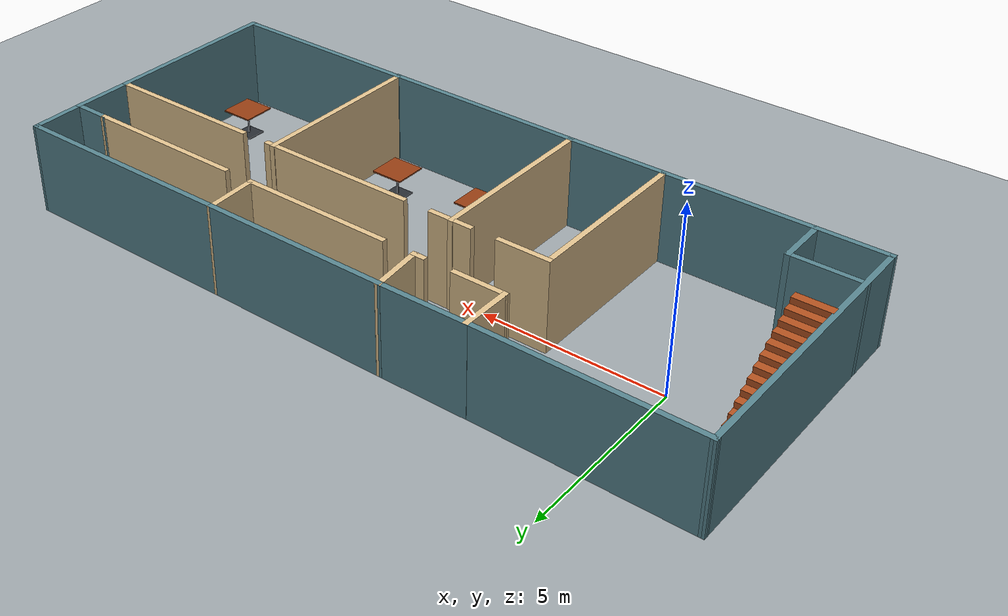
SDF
<?xml version="1.0" ?>
<sdf version='1.6'>
  <world name='default'>
    <light name='sun' type='directional'>
      <cast_shadows>1</cast_shadows>
      <pose>0 0 10 0 -0 0</pose>
      <diffuse>1 0.95 0.88 1</diffuse>
      <specular>0.25 0.25 0.25 1</specular>
      <attenuation>
        <range>1000</range>
        <constant>0.9</constant>
        <linear>0.01</linear>
        <quadratic>0.001</quadratic>
      </attenuation>
      <direction>0.5 0.1 -0.9</direction>
    </light>
    <scene>
      <ambient>0.68 0.68 0.68 1</ambient>
      <background>0.52 0.70 0.88 1</background>
      <shadows>1</shadows>
    </scene>
    <physics name='default_physics' default='0' type='ode'>
      <max_step_size>0.01</max_step_size>
      <real_time_factor>1</real_time_factor>
      <real_time_update_rate>100</real_time_update_rate>
    </physics>

    <!-- Gazebo Sim systems (ROS 2 / ros_gz) -->
    <plugin
      filename="gz-sim-physics-system"
      name="gz::sim::systems::Physics"/>

    <plugin
      filename="gz-sim-user-commands-system"
      name="gz::sim::systems::UserCommands"/>

    <plugin
      filename="gz-sim-scene-broadcaster-system"
      name="gz::sim::systems::SceneBroadcaster"/>

    <plugin
      filename="gz-sim-sensors-system"
      name="gz::sim::systems::Sensors">
      <render_engine>ogre2</render_engine>
    </plugin>
    <model name='ground_plane_0'>
      <static>1</static>
      <link name='link'>
        <collision name='collision'>
          <geometry>
            <plane>
              <normal>0 0 1</normal>
              <size>100 100</size>
            </plane>
          </geometry>
          <surface>
            <friction>
              <ode>
                <mu>100</mu>
                <mu2>50</mu2>
              </ode>
              <torsional>
                <ode/>
              </torsional>
            </friction>
            <bounce/>
            <contact>
              <ode/>
            </contact>
          </surface>
          <max_contacts>10</max_contacts>
        </collision>
        <visual name='visual'>
          <cast_shadows>0</cast_shadows>
          <geometry>
            <plane>
              <normal>0 0 1</normal>
              <size>100 100</size>
            </plane>
          </geometry>
          <material>
            <ambient>0.42 0.44 0.46 1</ambient>
            <diffuse>0.62 0.65 0.67 1</diffuse>
            <specular>0.08 0.08 0.08 1</specular>
            <emissive>0 0 0 1</emissive>
          </material>
        </visual>
        <velocity_decay>
          <linear>0</linear>
          <angular>0</angular>
        </velocity_decay>
        <self_collide>0</self_collide>
        <kinematic>0</kinematic>
        <gravity>1</gravity>
      </link>
      <pose>0.497681 0 0 0 -0 0</pose>
    </model>
    <gravity>0 0 -9.8</gravity>
    <magnetic_field>6e-06 2.3e-05 -4.2e-05</magnetic_field>
    <atmosphere type='adiabatic'/>
    <spherical_coordinates>
      <surface_model>EARTH_WGS84</surface_model>
      <latitude_deg>0</latitude_deg>
      <longitude_deg>0</longitude_deg>
      <elevation>0</elevation>
      <heading_deg>0</heading_deg>
    </spherical_coordinates>
    <model name='inco_planta_baja_0'>
      <link name='Stairs_0'>
        <pose>0 0 0 0 -0 0</pose>
        <self_collide>0</self_collide>
        <kinematic>0</kinematic>
        <visual name='Stairs_0_Visual_2'>
          <pose>-9.24623 1.59162 0.416667 0 -0 0</pose>
          <geometry>
            <box>
              <size>1 0.233333 0.166667</size>
            </box>
          </geometry>
                              <material>
            <ambient>0.25 0.12 0.05 1</ambient>
            <diffuse>0.70 0.32 0.12 1</diffuse>
            <specular>0.12 0.12 0.12 1</specular>
            <emissive>0 0 0 1</emissive>
          </material>
          <cast_shadows>1</cast_shadows>
          <transparency>0</transparency>
        </visual>
        <visual name='Stairs_0_Visual_0'>
          <pose>-9.24623 2.05829 0.083333 0 -0 0</pose>
          <geometry>
            <box>
              <size>1 0.233333 0.166667</size>
            </box>
          </geometry>
                              <material>
            <ambient>0.25 0.12 0.05 1</ambient>
            <diffuse>0.70 0.32 0.12 1</diffuse>
            <specular>0.12 0.12 0.12 1</specular>
            <emissive>0 0 0 1</emissive>
          </material>
          <cast_shadows>1</cast_shadows>
          <transparency>0</transparency>
        </visual>
        <visual name='Stairs_0_Visual_1'>
          <pose>-9.24623 1.82496 0.25 0 -0 0</pose>
          <geometry>
            <box>
              <size>1 0.233333 0.166667</size>
            </box>
          </geometry>
                              <material>
            <ambient>0.25 0.12 0.05 1</ambient>
            <diffuse>0.70 0.32 0.12 1</diffuse>
            <specular>0.12 0.12 0.12 1</specular>
            <emissive>0 0 0 1</emissive>
          </material>
          <cast_shadows>1</cast_shadows>
          <transparency>0</transparency>
        </visual>
        <visual name='Stairs_0_Visual_3'>
          <pose>-9.24623 1.35829 0.583333 0 -0 0</pose>
          <geometry>
            <box>
              <size>1 0.233333 0.166667</size>
            </box>
          </geometry>
                              <material>
            <ambient>0.25 0.12 0.05 1</ambient>
            <diffuse>0.70 0.32 0.12 1</diffuse>
            <specular>0.12 0.12 0.12 1</specular>
            <emissive>0 0 0 1</emissive>
          </material>
          <cast_shadows>1</cast_shadows>
          <transparency>0</transparency>
        </visual>
        <visual name='Stairs_0_Visual_4'>
          <pose>-9.24623 1.12495 0.75 0 -0 0</pose>
          <geometry>
            <box>
              <size>1 0.233333 0.166667</size>
            </box>
          </geometry>
                              <material>
            <ambient>0.25 0.12 0.05 1</ambient>
            <diffuse>0.70 0.32 0.12 1</diffuse>
            <specular>0.12 0.12 0.12 1</specular>
            <emissive>0 0 0 1</emissive>
          </material>
          <cast_shadows>1</cast_shadows>
          <transparency>0</transparency>
        </visual>
        <visual name='Stairs_0_Visual_5'>
          <pose>-9.24623 0.891622 0.916667 0 -0 0</pose>
          <geometry>
            <box>
              <size>1 0.233333 0.166667</size>
            </box>
          </geometry>
                              <material>
            <ambient>0.25 0.12 0.05 1</ambient>
            <diffuse>0.70 0.32 0.12 1</diffuse>
            <specular>0.12 0.12 0.12 1</specular>
            <emissive>0 0 0 1</emissive>
          </material>
          <cast_shadows>1</cast_shadows>
          <transparency>0</transparency>
        </visual>
        <visual name='Stairs_0_Visual_6'>
          <pose>-9.24623 0.658289 1.08333 0 -0 0</pose>
          <geometry>
            <box>
              <size>1 0.233333 0.166667</size>
            </box>
          </geometry>
                              <material>
            <ambient>0.25 0.12 0.05 1</ambient>
            <diffuse>0.70 0.32 0.12 1</diffuse>
            <specular>0.12 0.12 0.12 1</specular>
            <emissive>0 0 0 1</emissive>
          </material>
          <cast_shadows>1</cast_shadows>
          <transparency>0</transparency>
        </visual>
        <visual name='Stairs_0_Visual_8'>
          <pose>-9.24623 0.191622 1.41667 0 -0 0</pose>
          <geometry>
            <box>
              <size>1 0.233333 0.166667</size>
            </box>
          </geometry>
                              <material>
            <ambient>0.25 0.12 0.05 1</ambient>
            <diffuse>0.70 0.32 0.12 1</diffuse>
            <specular>0.12 0.12 0.12 1</specular>
            <emissive>0 0 0 1</emissive>
          </material>
          <cast_shadows>1</cast_shadows>
          <transparency>0</transparency>
        </visual>
        <visual name='Stairs_0_Visual_7'>
          <pose>-9.24623 0.424955 1.25 0 -0 0</pose>
          <geometry>
            <box>
              <size>1 0.233333 0.166667</size>
            </box>
          </geometry>
                              <material>
            <ambient>0.25 0.12 0.05 1</ambient>
            <diffuse>0.70 0.32 0.12 1</diffuse>
            <specular>0.12 0.12 0.12 1</specular>
            <emissive>0 0 0 1</emissive>
          </material>
          <cast_shadows>1</cast_shadows>
          <transparency>0</transparency>
        </visual>
        <visual name='Stairs_0_Visual_9'>
          <pose>-9.24623 -0.041711 1.58333 0 -0 0</pose>
          <geometry>
            <box>
              <size>1 0.233333 0.166667</size>
            </box>
          </geometry>
                              <material>
            <ambient>0.25 0.12 0.05 1</ambient>
            <diffuse>0.70 0.32 0.12 1</diffuse>
            <specular>0.12 0.12 0.12 1</specular>
            <emissive>0 0 0 1</emissive>
          </material>
          <cast_shadows>1</cast_shadows>
          <transparency>0</transparency>
        </visual>
        <visual name='Stairs_0_Visual_10'>
          <pose>-9.24623 -0.275045 1.75 0 -0 0</pose>
          <geometry>
            <box>
              <size>1 0.233333 0.166667</size>
            </box>
          </geometry>
                              <material>
            <ambient>0.25 0.12 0.05 1</ambient>
            <diffuse>0.70 0.32 0.12 1</diffuse>
            <specular>0.12 0.12 0.12 1</specular>
            <emissive>0 0 0 1</emissive>
          </material>
          <cast_shadows>1</cast_shadows>
          <transparency>0</transparency>
        </visual>
        <visual name='Stairs_0_Visual_11'>
          <pose>-9.24623 -0.508378 1.91667 0 -0 0</pose>
          <geometry>
            <box>
              <size>1 0.233333 0.166667</size>
            </box>
          </geometry>
                              <material>
            <ambient>0.25 0.12 0.05 1</ambient>
            <diffuse>0.70 0.32 0.12 1</diffuse>
            <specular>0.12 0.12 0.12 1</specular>
            <emissive>0 0 0 1</emissive>
          </material>
          <cast_shadows>1</cast_shadows>
          <transparency>0</transparency>
        </visual>
        <visual name='Stairs_0_Visual_12'>
          <pose>-9.24623 -0.741711 2.08333 0 -0 0</pose>
          <geometry>
            <box>
              <size>1 0.233333 0.166667</size>
            </box>
          </geometry>
                              <material>
            <ambient>0.25 0.12 0.05 1</ambient>
            <diffuse>0.70 0.32 0.12 1</diffuse>
            <specular>0.12 0.12 0.12 1</specular>
            <emissive>0 0 0 1</emissive>
          </material>
          <cast_shadows>1</cast_shadows>
          <transparency>0</transparency>
        </visual>
        <visual name='Stairs_0_Visual_13'>
          <pose>-9.24623 -0.975045 2.25 0 -0 0</pose>
          <geometry>
            <box>
              <size>1 0.233333 0.166667</size>
            </box>
          </geometry>
                              <material>
            <ambient>0.25 0.12 0.05 1</ambient>
            <diffuse>0.70 0.32 0.12 1</diffuse>
            <specular>0.12 0.12 0.12 1</specular>
            <emissive>0 0 0 1</emissive>
          </material>
          <cast_shadows>1</cast_shadows>
          <transparency>0</transparency>
        </visual>
        <visual name='Stairs_0_Visual_14'>
          <pose>-9.24623 -1.20838 2.41667 0 -0 0</pose>
          <geometry>
            <box>
              <size>1 0.233333 0.166667</size>
            </box>
          </geometry>
                              <material>
            <ambient>0.25 0.12 0.05 1</ambient>
            <diffuse>0.70 0.32 0.12 1</diffuse>
            <specular>0.12 0.12 0.12 1</specular>
            <emissive>0 0 0 1</emissive>
          </material>
          <cast_shadows>1</cast_shadows>
          <transparency>0</transparency>
        </visual>
        <collision name='Stairs_0_Collision_0'>
          <laser_retro>0</laser_retro>
          <max_contacts>10</max_contacts>
          <pose>-9.24623 2.05829 0.083333 0 -0 0</pose>
          <geometry>
            <box>
              <size>1 0.233333 0.166667</size>
            </box>
          </geometry>
          <surface>
            <friction>
              <ode>
                <mu>1</mu>
                <mu2>1</mu2>
                <fdir1>0 0 0</fdir1>
                <slip1>0</slip1>
                <slip2>0</slip2>
              </ode>
              <torsional>
                <coefficient>1</coefficient>
                <patch_radius>0</patch_radius>
                <surface_radius>0</surface_radius>
                <use_patch_radius>1</use_patch_radius>
                <ode>
                  <slip>0</slip>
                </ode>
              </torsional>
            </friction>
            <bounce>
              <restitution_coefficient>0</restitution_coefficient>
              <threshold>1e+06</threshold>
            </bounce>
            <contact>
              <collide_without_contact>0</collide_without_contact>
              <collide_without_contact_bitmask>1</collide_without_contact_bitmask>
              <collide_bitmask>1</collide_bitmask>
              <ode>
                <soft_cfm>0</soft_cfm>
                <soft_erp>0.2</soft_erp>
                <kp>1e+13</kp>
                <kd>1</kd>
                <max_vel>0.01</max_vel>
                <min_depth>0</min_depth>
              </ode>
              <bullet>
                <split_impulse>1</split_impulse>
                <split_impulse_penetration_threshold>-0.01</split_impulse_penetration_threshold>
                <soft_cfm>0</soft_cfm>
                <soft_erp>0.2</soft_erp>
                <kp>1e+13</kp>
                <kd>1</kd>
              </bullet>
            </contact>
          </surface>
        </collision>
        <collision name='Stairs_0_Collision_1'>
          <laser_retro>0</laser_retro>
          <max_contacts>10</max_contacts>
          <pose>-9.24623 1.82496 0.25 0 -0 0</pose>
          <geometry>
            <box>
              <size>1 0.233333 0.166667</size>
            </box>
          </geometry>
          <surface>
            <friction>
              <ode>
                <mu>1</mu>
                <mu2>1</mu2>
                <fdir1>0 0 0</fdir1>
                <slip1>0</slip1>
                <slip2>0</slip2>
              </ode>
              <torsional>
                <coefficient>1</coefficient>
                <patch_radius>0</patch_radius>
                <surface_radius>0</surface_radius>
                <use_patch_radius>1</use_patch_radius>
                <ode>
                  <slip>0</slip>
                </ode>
              </torsional>
            </friction>
            <bounce>
              <restitution_coefficient>0</restitution_coefficient>
              <threshold>1e+06</threshold>
            </bounce>
            <contact>
              <collide_without_contact>0</collide_without_contact>
              <collide_without_contact_bitmask>1</collide_without_contact_bitmask>
              <collide_bitmask>1</collide_bitmask>
              <ode>
                <soft_cfm>0</soft_cfm>
                <soft_erp>0.2</soft_erp>
                <kp>1e+13</kp>
                <kd>1</kd>
                <max_vel>0.01</max_vel>
                <min_depth>0</min_depth>
              </ode>
              <bullet>
                <split_impulse>1</split_impulse>
                <split_impulse_penetration_threshold>-0.01</split_impulse_penetration_threshold>
                <soft_cfm>0</soft_cfm>
                <soft_erp>0.2</soft_erp>
                <kp>1e+13</kp>
                <kd>1</kd>
              </bullet>
            </contact>
          </surface>
        </collision>
        <collision name='Stairs_0_Collision_7'>
          <laser_retro>0</laser_retro>
          <max_contacts>10</max_contacts>
          <pose>-9.24623 0.424955 1.25 0 -0 0</pose>
          <geometry>
            <box>
              <size>1 0.233333 0.166667</size>
            </box>
          </geometry>
          <surface>
            <friction>
              <ode>
                <mu>1</mu>
                <mu2>1</mu2>
                <fdir1>0 0 0</fdir1>
                <slip1>0</slip1>
                <slip2>0</slip2>
              </ode>
              <torsional>
                <coefficient>1</coefficient>
                <patch_radius>0</patch_radius>
                <surface_radius>0</surface_radius>
                <use_patch_radius>1</use_patch_radius>
                <ode>
                  <slip>0</slip>
                </ode>
              </torsional>
            </friction>
            <bounce>
              <restitution_coefficient>0</restitution_coefficient>
              <threshold>1e+06</threshold>
            </bounce>
            <contact>
              <collide_without_contact>0</collide_without_contact>
              <collide_without_contact_bitmask>1</collide_without_contact_bitmask>
              <collide_bitmask>1</collide_bitmask>
              <ode>
                <soft_cfm>0</soft_cfm>
                <soft_erp>0.2</soft_erp>
                <kp>1e+13</kp>
                <kd>1</kd>
                <max_vel>0.01</max_vel>
                <min_depth>0</min_depth>
              </ode>
              <bullet>
                <split_impulse>1</split_impulse>
                <split_impulse_penetration_threshold>-0.01</split_impulse_penetration_threshold>
                <soft_cfm>0</soft_cfm>
                <soft_erp>0.2</soft_erp>
                <kp>1e+13</kp>
                <kd>1</kd>
              </bullet>
            </contact>
          </surface>
        </collision>
        <collision name='Stairs_0_Collision_2'>
          <laser_retro>0</laser_retro>
          <max_contacts>10</max_contacts>
          <pose>-9.24623 1.59162 0.416667 0 -0 0</pose>
          <geometry>
            <box>
              <size>1 0.233333 0.166667</size>
            </box>
          </geometry>
          <surface>
            <friction>
              <ode>
                <mu>1</mu>
                <mu2>1</mu2>
                <fdir1>0 0 0</fdir1>
                <slip1>0</slip1>
                <slip2>0</slip2>
              </ode>
              <torsional>
                <coefficient>1</coefficient>
                <patch_radius>0</patch_radius>
                <surface_radius>0</surface_radius>
                <use_patch_radius>1</use_patch_radius>
                <ode>
                  <slip>0</slip>
                </ode>
              </torsional>
            </friction>
            <bounce>
              <restitution_coefficient>0</restitution_coefficient>
              <threshold>1e+06</threshold>
            </bounce>
            <contact>
              <collide_without_contact>0</collide_without_contact>
              <collide_without_contact_bitmask>1</collide_without_contact_bitmask>
              <collide_bitmask>1</collide_bitmask>
              <ode>
                <soft_cfm>0</soft_cfm>
                <soft_erp>0.2</soft_erp>
                <kp>1e+13</kp>
                <kd>1</kd>
                <max_vel>0.01</max_vel>
                <min_depth>0</min_depth>
              </ode>
              <bullet>
                <split_impulse>1</split_impulse>
                <split_impulse_penetration_threshold>-0.01</split_impulse_penetration_threshold>
                <soft_cfm>0</soft_cfm>
                <soft_erp>0.2</soft_erp>
                <kp>1e+13</kp>
                <kd>1</kd>
              </bullet>
            </contact>
          </surface>
        </collision>
        <collision name='Stairs_0_Collision_3'>
          <laser_retro>0</laser_retro>
          <max_contacts>10</max_contacts>
          <pose>-9.24623 1.35829 0.583333 0 -0 0</pose>
          <geometry>
            <box>
              <size>1 0.233333 0.166667</size>
            </box>
          </geometry>
          <surface>
            <friction>
              <ode>
                <mu>1</mu>
                <mu2>1</mu2>
                <fdir1>0 0 0</fdir1>
                <slip1>0</slip1>
                <slip2>0</slip2>
              </ode>
              <torsional>
                <coefficient>1</coefficient>
                <patch_radius>0</patch_radius>
                <surface_radius>0</surface_radius>
                <use_patch_radius>1</use_patch_radius>
                <ode>
                  <slip>0</slip>
                </ode>
              </torsional>
            </friction>
            <bounce>
              <restitution_coefficient>0</restitution_coefficient>
              <threshold>1e+06</threshold>
            </bounce>
            <contact>
              <collide_without_contact>0</collide_without_contact>
              <collide_without_contact_bitmask>1</collide_without_contact_bitmask>
              <collide_bitmask>1</collide_bitmask>
              <ode>
                <soft_cfm>0</soft_cfm>
                <soft_erp>0.2</soft_erp>
                <kp>1e+13</kp>
                <kd>1</kd>
                <max_vel>0.01</max_vel>
                <min_depth>0</min_depth>
              </ode>
              <bullet>
                <split_impulse>1</split_impulse>
                <split_impulse_penetration_threshold>-0.01</split_impulse_penetration_threshold>
                <soft_cfm>0</soft_cfm>
                <soft_erp>0.2</soft_erp>
                <kp>1e+13</kp>
                <kd>1</kd>
              </bullet>
            </contact>
          </surface>
        </collision>
        <collision name='Stairs_0_Collision_4'>
          <laser_retro>0</laser_retro>
          <max_contacts>10</max_contacts>
          <pose>-9.24623 1.12495 0.75 0 -0 0</pose>
          <geometry>
            <box>
              <size>1 0.233333 0.166667</size>
            </box>
          </geometry>
          <surface>
            <friction>
              <ode>
                <mu>1</mu>
                <mu2>1</mu2>
                <fdir1>0 0 0</fdir1>
                <slip1>0</slip1>
                <slip2>0</slip2>
              </ode>
              <torsional>
                <coefficient>1</coefficient>
                <patch_radius>0</patch_radius>
                <surface_radius>0</surface_radius>
                <use_patch_radius>1</use_patch_radius>
                <ode>
                  <slip>0</slip>
                </ode>
              </torsional>
            </friction>
            <bounce>
              <restitution_coefficient>0</restitution_coefficient>
              <threshold>1e+06</threshold>
            </bounce>
            <contact>
              <collide_without_contact>0</collide_without_contact>
              <collide_without_contact_bitmask>1</collide_without_contact_bitmask>
              <collide_bitmask>1</collide_bitmask>
              <ode>
                <soft_cfm>0</soft_cfm>
                <soft_erp>0.2</soft_erp>
                <kp>1e+13</kp>
                <kd>1</kd>
                <max_vel>0.01</max_vel>
                <min_depth>0</min_depth>
              </ode>
              <bullet>
                <split_impulse>1</split_impulse>
                <split_impulse_penetration_threshold>-0.01</split_impulse_penetration_threshold>
                <soft_cfm>0</soft_cfm>
                <soft_erp>0.2</soft_erp>
                <kp>1e+13</kp>
                <kd>1</kd>
              </bullet>
            </contact>
          </surface>
        </collision>
        <collision name='Stairs_0_Collision_5'>
          <laser_retro>0</laser_retro>
          <max_contacts>10</max_contacts>
          <pose>-9.24623 0.891622 0.916667 0 -0 0</pose>
          <geometry>
            <box>
              <size>1 0.233333 0.166667</size>
            </box>
          </geometry>
          <surface>
            <friction>
              <ode>
                <mu>1</mu>
                <mu2>1</mu2>
                <fdir1>0 0 0</fdir1>
                <slip1>0</slip1>
                <slip2>0</slip2>
              </ode>
              <torsional>
                <coefficient>1</coefficient>
                <patch_radius>0</patch_radius>
                <surface_radius>0</surface_radius>
                <use_patch_radius>1</use_patch_radius>
                <ode>
                  <slip>0</slip>
                </ode>
              </torsional>
            </friction>
            <bounce>
              <restitution_coefficient>0</restitution_coefficient>
              <threshold>1e+06</threshold>
            </bounce>
            <contact>
              <collide_without_contact>0</collide_without_contact>
              <collide_without_contact_bitmask>1</collide_without_contact_bitmask>
              <collide_bitmask>1</collide_bitmask>
              <ode>
                <soft_cfm>0</soft_cfm>
                <soft_erp>0.2</soft_erp>
                <kp>1e+13</kp>
                <kd>1</kd>
                <max_vel>0.01</max_vel>
                <min_depth>0</min_depth>
              </ode>
              <bullet>
                <split_impulse>1</split_impulse>
                <split_impulse_penetration_threshold>-0.01</split_impulse_penetration_threshold>
                <soft_cfm>0</soft_cfm>
                <soft_erp>0.2</soft_erp>
                <kp>1e+13</kp>
                <kd>1</kd>
              </bullet>
            </contact>
          </surface>
        </collision>
        <collision name='Stairs_0_Collision_6'>
          <laser_retro>0</laser_retro>
          <max_contacts>10</max_contacts>
          <pose>-9.24623 0.658289 1.08333 0 -0 0</pose>
          <geometry>
            <box>
              <size>1 0.233333 0.166667</size>
            </box>
          </geometry>
          <surface>
            <friction>
              <ode>
                <mu>1</mu>
                <mu2>1</mu2>
                <fdir1>0 0 0</fdir1>
                <slip1>0</slip1>
                <slip2>0</slip2>
              </ode>
              <torsional>
                <coefficient>1</coefficient>
                <patch_radius>0</patch_radius>
                <surface_radius>0</surface_radius>
                <use_patch_radius>1</use_patch_radius>
                <ode>
                  <slip>0</slip>
                </ode>
              </torsional>
            </friction>
            <bounce>
              <restitution_coefficient>0</restitution_coefficient>
              <threshold>1e+06</threshold>
            </bounce>
            <contact>
              <collide_without_contact>0</collide_without_contact>
              <collide_without_contact_bitmask>1</collide_without_contact_bitmask>
              <collide_bitmask>1</collide_bitmask>
              <ode>
                <soft_cfm>0</soft_cfm>
                <soft_erp>0.2</soft_erp>
                <kp>1e+13</kp>
                <kd>1</kd>
                <max_vel>0.01</max_vel>
                <min_depth>0</min_depth>
              </ode>
              <bullet>
                <split_impulse>1</split_impulse>
                <split_impulse_penetration_threshold>-0.01</split_impulse_penetration_threshold>
                <soft_cfm>0</soft_cfm>
                <soft_erp>0.2</soft_erp>
                <kp>1e+13</kp>
                <kd>1</kd>
              </bullet>
            </contact>
          </surface>
        </collision>
        <collision name='Stairs_0_Collision_8'>
          <laser_retro>0</laser_retro>
          <max_contacts>10</max_contacts>
          <pose>-9.24623 0.191622 1.41667 0 -0 0</pose>
          <geometry>
            <box>
              <size>1 0.233333 0.166667</size>
            </box>
          </geometry>
          <surface>
            <friction>
              <ode>
                <mu>1</mu>
                <mu2>1</mu2>
                <fdir1>0 0 0</fdir1>
                <slip1>0</slip1>
                <slip2>0</slip2>
              </ode>
              <torsional>
                <coefficient>1</coefficient>
                <patch_radius>0</patch_radius>
                <surface_radius>0</surface_radius>
                <use_patch_radius>1</use_patch_radius>
                <ode>
                  <slip>0</slip>
                </ode>
              </torsional>
            </friction>
            <bounce>
              <restitution_coefficient>0</restitution_coefficient>
              <threshold>1e+06</threshold>
            </bounce>
            <contact>
              <collide_without_contact>0</collide_without_contact>
              <collide_without_contact_bitmask>1</collide_without_contact_bitmask>
              <collide_bitmask>1</collide_bitmask>
              <ode>
                <soft_cfm>0</soft_cfm>
                <soft_erp>0.2</soft_erp>
                <kp>1e+13</kp>
                <kd>1</kd>
                <max_vel>0.01</max_vel>
                <min_depth>0</min_depth>
              </ode>
              <bullet>
                <split_impulse>1</split_impulse>
                <split_impulse_penetration_threshold>-0.01</split_impulse_penetration_threshold>
                <soft_cfm>0</soft_cfm>
                <soft_erp>0.2</soft_erp>
                <kp>1e+13</kp>
                <kd>1</kd>
              </bullet>
            </contact>
          </surface>
        </collision>
        <collision name='Stairs_0_Collision_9'>
          <laser_retro>0</laser_retro>
          <max_contacts>10</max_contacts>
          <pose>-9.24623 -0.041711 1.58333 0 -0 0</pose>
          <geometry>
            <box>
              <size>1 0.233333 0.166667</size>
            </box>
          </geometry>
          <surface>
            <friction>
              <ode>
                <mu>1</mu>
                <mu2>1</mu2>
                <fdir1>0 0 0</fdir1>
                <slip1>0</slip1>
                <slip2>0</slip2>
              </ode>
              <torsional>
                <coefficient>1</coefficient>
                <patch_radius>0</patch_radius>
                <surface_radius>0</surface_radius>
                <use_patch_radius>1</use_patch_radius>
                <ode>
                  <slip>0</slip>
                </ode>
              </torsional>
            </friction>
            <bounce>
              <restitution_coefficient>0</restitution_coefficient>
              <threshold>1e+06</threshold>
            </bounce>
            <contact>
              <collide_without_contact>0</collide_without_contact>
              <collide_without_contact_bitmask>1</collide_without_contact_bitmask>
              <collide_bitmask>1</collide_bitmask>
              <ode>
                <soft_cfm>0</soft_cfm>
                <soft_erp>0.2</soft_erp>
                <kp>1e+13</kp>
                <kd>1</kd>
                <max_vel>0.01</max_vel>
                <min_depth>0</min_depth>
              </ode>
              <bullet>
                <split_impulse>1</split_impulse>
                <split_impulse_penetration_threshold>-0.01</split_impulse_penetration_threshold>
                <soft_cfm>0</soft_cfm>
                <soft_erp>0.2</soft_erp>
                <kp>1e+13</kp>
                <kd>1</kd>
              </bullet>
            </contact>
          </surface>
        </collision>
        <collision name='Stairs_0_Collision_10'>
          <laser_retro>0</laser_retro>
          <max_contacts>10</max_contacts>
          <pose>-9.24623 -0.275045 1.75 0 -0 0</pose>
          <geometry>
            <box>
              <size>1 0.233333 0.166667</size>
            </box>
          </geometry>
          <surface>
            <friction>
              <ode>
                <mu>1</mu>
                <mu2>1</mu2>
                <fdir1>0 0 0</fdir1>
                <slip1>0</slip1>
                <slip2>0</slip2>
              </ode>
              <torsional>
                <coefficient>1</coefficient>
                <patch_radius>0</patch_radius>
                <surface_radius>0</surface_radius>
                <use_patch_radius>1</use_patch_radius>
                <ode>
                  <slip>0</slip>
                </ode>
              </torsional>
            </friction>
            <bounce>
              <restitution_coefficient>0</restitution_coefficient>
              <threshold>1e+06</threshold>
            </bounce>
            <contact>
              <collide_without_contact>0</collide_without_contact>
              <collide_without_contact_bitmask>1</collide_without_contact_bitmask>
              <collide_bitmask>1</collide_bitmask>
              <ode>
                <soft_cfm>0</soft_cfm>
                <soft_erp>0.2</soft_erp>
                <kp>1e+13</kp>
                <kd>1</kd>
                <max_vel>0.01</max_vel>
                <min_depth>0</min_depth>
              </ode>
              <bullet>
                <split_impulse>1</split_impulse>
                <split_impulse_penetration_threshold>-0.01</split_impulse_penetration_threshold>
                <soft_cfm>0</soft_cfm>
                <soft_erp>0.2</soft_erp>
                <kp>1e+13</kp>
                <kd>1</kd>
              </bullet>
            </contact>
          </surface>
        </collision>
        <collision name='Stairs_0_Collision_11'>
          <laser_retro>0</laser_retro>
          <max_contacts>10</max_contacts>
          <pose>-9.24623 -0.508378 1.91667 0 -0 0</pose>
          <geometry>
            <box>
              <size>1 0.233333 0.166667</size>
            </box>
          </geometry>
          <surface>
            <friction>
              <ode>
                <mu>1</mu>
                <mu2>1</mu2>
                <fdir1>0 0 0</fdir1>
                <slip1>0</slip1>
                <slip2>0</slip2>
              </ode>
              <torsional>
                <coefficient>1</coefficient>
                <patch_radius>0</patch_radius>
                <surface_radius>0</surface_radius>
                <use_patch_radius>1</use_patch_radius>
                <ode>
                  <slip>0</slip>
                </ode>
              </torsional>
            </friction>
            <bounce>
              <restitution_coefficient>0</restitution_coefficient>
              <threshold>1e+06</threshold>
            </bounce>
            <contact>
              <collide_without_contact>0</collide_without_contact>
              <collide_without_contact_bitmask>1</collide_without_contact_bitmask>
              <collide_bitmask>1</collide_bitmask>
              <ode>
                <soft_cfm>0</soft_cfm>
                <soft_erp>0.2</soft_erp>
                <kp>1e+13</kp>
                <kd>1</kd>
                <max_vel>0.01</max_vel>
                <min_depth>0</min_depth>
              </ode>
              <bullet>
                <split_impulse>1</split_impulse>
                <split_impulse_penetration_threshold>-0.01</split_impulse_penetration_threshold>
                <soft_cfm>0</soft_cfm>
                <soft_erp>0.2</soft_erp>
                <kp>1e+13</kp>
                <kd>1</kd>
              </bullet>
            </contact>
          </surface>
        </collision>
        <collision name='Stairs_0_Collision_13'>
          <laser_retro>0</laser_retro>
          <max_contacts>10</max_contacts>
          <pose>-9.24623 -0.975045 2.25 0 -0 0</pose>
          <geometry>
            <box>
              <size>1 0.233333 0.166667</size>
            </box>
          </geometry>
          <surface>
            <friction>
              <ode>
                <mu>1</mu>
                <mu2>1</mu2>
                <fdir1>0 0 0</fdir1>
                <slip1>0</slip1>
                <slip2>0</slip2>
              </ode>
              <torsional>
                <coefficient>1</coefficient>
                <patch_radius>0</patch_radius>
                <surface_radius>0</surface_radius>
                <use_patch_radius>1</use_patch_radius>
                <ode>
                  <slip>0</slip>
                </ode>
              </torsional>
            </friction>
            <bounce>
              <restitution_coefficient>0</restitution_coefficient>
              <threshold>1e+06</threshold>
            </bounce>
            <contact>
              <collide_without_contact>0</collide_without_contact>
              <collide_without_contact_bitmask>1</collide_without_contact_bitmask>
              <collide_bitmask>1</collide_bitmask>
              <ode>
                <soft_cfm>0</soft_cfm>
                <soft_erp>0.2</soft_erp>
                <kp>1e+13</kp>
                <kd>1</kd>
                <max_vel>0.01</max_vel>
                <min_depth>0</min_depth>
              </ode>
              <bullet>
                <split_impulse>1</split_impulse>
                <split_impulse_penetration_threshold>-0.01</split_impulse_penetration_threshold>
                <soft_cfm>0</soft_cfm>
                <soft_erp>0.2</soft_erp>
                <kp>1e+13</kp>
                <kd>1</kd>
              </bullet>
            </contact>
          </surface>
        </collision>
        <collision name='Stairs_0_Collision_12'>
          <laser_retro>0</laser_retro>
          <max_contacts>10</max_contacts>
          <pose>-9.24623 -0.741711 2.08333 0 -0 0</pose>
          <geometry>
            <box>
              <size>1 0.233333 0.166667</size>
            </box>
          </geometry>
          <surface>
            <friction>
              <ode>
                <mu>1</mu>
                <mu2>1</mu2>
                <fdir1>0 0 0</fdir1>
                <slip1>0</slip1>
                <slip2>0</slip2>
              </ode>
              <torsional>
                <coefficient>1</coefficient>
                <patch_radius>0</patch_radius>
                <surface_radius>0</surface_radius>
                <use_patch_radius>1</use_patch_radius>
                <ode>
                  <slip>0</slip>
                </ode>
              </torsional>
            </friction>
            <bounce>
              <restitution_coefficient>0</restitution_coefficient>
              <threshold>1e+06</threshold>
            </bounce>
            <contact>
              <collide_without_contact>0</collide_without_contact>
              <collide_without_contact_bitmask>1</collide_without_contact_bitmask>
              <collide_bitmask>1</collide_bitmask>
              <ode>
                <soft_cfm>0</soft_cfm>
                <soft_erp>0.2</soft_erp>
                <kp>1e+13</kp>
                <kd>1</kd>
                <max_vel>0.01</max_vel>
                <min_depth>0</min_depth>
              </ode>
              <bullet>
                <split_impulse>1</split_impulse>
                <split_impulse_penetration_threshold>-0.01</split_impulse_penetration_threshold>
                <soft_cfm>0</soft_cfm>
                <soft_erp>0.2</soft_erp>
                <kp>1e+13</kp>
                <kd>1</kd>
              </bullet>
            </contact>
          </surface>
        </collision>
        <collision name='Stairs_0_Collision_14'>
          <laser_retro>0</laser_retro>
          <max_contacts>10</max_contacts>
          <pose>-9.24623 -1.20838 2.41667 0 -0 0</pose>
          <geometry>
            <box>
              <size>1 0.233333 0.166667</size>
            </box>
          </geometry>
          <surface>
            <friction>
              <ode>
                <mu>1</mu>
                <mu2>1</mu2>
                <fdir1>0 0 0</fdir1>
                <slip1>0</slip1>
                <slip2>0</slip2>
              </ode>
              <torsional>
                <coefficient>1</coefficient>
                <patch_radius>0</patch_radius>
                <surface_radius>0</surface_radius>
                <use_patch_radius>1</use_patch_radius>
                <ode>
                  <slip>0</slip>
                </ode>
              </torsional>
            </friction>
            <bounce>
              <restitution_coefficient>0</restitution_coefficient>
              <threshold>1e+06</threshold>
            </bounce>
            <contact>
              <collide_without_contact>0</collide_without_contact>
              <collide_without_contact_bitmask>1</collide_without_contact_bitmask>
              <collide_bitmask>1</collide_bitmask>
              <ode>
                <soft_cfm>0</soft_cfm>
                <soft_erp>0.2</soft_erp>
                <kp>1e+13</kp>
                <kd>1</kd>
                <max_vel>0.01</max_vel>
                <min_depth>0</min_depth>
              </ode>
              <bullet>
                <split_impulse>1</split_impulse>
                <split_impulse_penetration_threshold>-0.01</split_impulse_penetration_threshold>
                <soft_cfm>0</soft_cfm>
                <soft_erp>0.2</soft_erp>
                <kp>1e+13</kp>
                <kd>1</kd>
              </bullet>
            </contact>
          </surface>
        </collision>
        <gravity>1</gravity>
      </link>
      <link name='Wall_10'>
        <pose>-3.93462 3.232 0 0 0 -1.5727</pose>
        <self_collide>0</self_collide>
        <kinematic>0</kinematic>
        <visual name='Wall_10_Visual'>
          <pose>0 0 1.25 0 -0 0</pose>
          <geometry>
            <box>
              <size>1.48163 0.15 2.5</size>
            </box>
          </geometry>
                              <material>
            <ambient>0.55 0.48 0.36 1</ambient>
            <diffuse>0.88 0.76 0.56 1</diffuse>
            <specular>0.05 0.05 0.05 1</specular>
            <emissive>0 0 0 1</emissive>
          </material>
          <cast_shadows>1</cast_shadows>
          <transparency>0</transparency>
        </visual>
        <collision name='Wall_10_Collision'>
          <laser_retro>0</laser_retro>
          <max_contacts>10</max_contacts>
          <pose>0 0 1.25 0 -0 0</pose>
          <geometry>
            <box>
              <size>1.48163 0.15 2.5</size>
            </box>
          </geometry>
          <surface>
            <friction>
              <ode>
                <mu>1</mu>
                <mu2>1</mu2>
                <fdir1>0 0 0</fdir1>
                <slip1>0</slip1>
                <slip2>0</slip2>
              </ode>
              <torsional>
                <coefficient>1</coefficient>
                <patch_radius>0</patch_radius>
                <surface_radius>0</surface_radius>
                <use_patch_radius>1</use_patch_radius>
                <ode>
                  <slip>0</slip>
                </ode>
              </torsional>
            </friction>
            <bounce>
              <restitution_coefficient>0</restitution_coefficient>
              <threshold>1e+06</threshold>
            </bounce>
            <contact>
              <collide_without_contact>0</collide_without_contact>
              <collide_without_contact_bitmask>1</collide_without_contact_bitmask>
              <collide_bitmask>1</collide_bitmask>
              <ode>
                <soft_cfm>0</soft_cfm>
                <soft_erp>0.2</soft_erp>
                <kp>1e+13</kp>
                <kd>1</kd>
                <max_vel>0.01</max_vel>
                <min_depth>0</min_depth>
              </ode>
              <bullet>
                <split_impulse>1</split_impulse>
                <split_impulse_penetration_threshold>-0.01</split_impulse_penetration_threshold>
                <soft_cfm>0</soft_cfm>
                <soft_erp>0.2</soft_erp>
                <kp>1e+13</kp>
                <kd>1</kd>
              </bullet>
            </contact>
          </surface>
        </collision>
        <gravity>1</gravity>
      </link>
      <link name='Wall_12'>
        <pose>-3.26089 2.56618 0 0 -0 0</pose>
        <self_collide>0</self_collide>
        <kinematic>0</kinematic>
        <visual name='Wall_12_Visual'>
          <pose>0 0 1.25 0 -0 0</pose>
          <geometry>
            <box>
              <size>1.5 0.15 2.5</size>
            </box>
          </geometry>
                              <material>
            <ambient>0.55 0.48 0.36 1</ambient>
            <diffuse>0.88 0.76 0.56 1</diffuse>
            <specular>0.05 0.05 0.05 1</specular>
            <emissive>0 0 0 1</emissive>
          </material>
          <cast_shadows>1</cast_shadows>
          <transparency>0</transparency>
        </visual>
        <collision name='Wall_12_Collision'>
          <laser_retro>0</laser_retro>
          <max_contacts>10</max_contacts>
          <pose>0 0 1.25 0 -0 0</pose>
          <geometry>
            <box>
              <size>1.5 0.15 2.5</size>
            </box>
          </geometry>
          <surface>
            <friction>
              <ode>
                <mu>1</mu>
                <mu2>1</mu2>
                <fdir1>0 0 0</fdir1>
                <slip1>0</slip1>
                <slip2>0</slip2>
              </ode>
              <torsional>
                <coefficient>1</coefficient>
                <patch_radius>0</patch_radius>
                <surface_radius>0</surface_radius>
                <use_patch_radius>1</use_patch_radius>
                <ode>
                  <slip>0</slip>
                </ode>
              </torsional>
            </friction>
            <bounce>
              <restitution_coefficient>0</restitution_coefficient>
              <threshold>1e+06</threshold>
            </bounce>
            <contact>
              <collide_without_contact>0</collide_without_contact>
              <collide_without_contact_bitmask>1</collide_without_contact_bitmask>
              <collide_bitmask>1</collide_bitmask>
              <ode>
                <soft_cfm>0</soft_cfm>
                <soft_erp>0.2</soft_erp>
                <kp>1e+13</kp>
                <kd>1</kd>
                <max_vel>0.01</max_vel>
                <min_depth>0</min_depth>
              </ode>
              <bullet>
                <split_impulse>1</split_impulse>
                <split_impulse_penetration_threshold>-0.01</split_impulse_penetration_threshold>
                <soft_cfm>0</soft_cfm>
                <soft_erp>0.2</soft_erp>
                <kp>1e+13</kp>
                <kd>1</kd>
              </bullet>
            </contact>
          </surface>
        </collision>
        <gravity>1</gravity>
      </link>
      <link name='Wall_126'>
        <pose>9.78501 1.72965 0 0 -0 1.5708</pose>
        <self_collide>0</self_collide>
        <kinematic>0</kinematic>
        <visual name='Wall_126_Visual'>
          <pose>0 0 1.25 0 -0 0</pose>
          <geometry>
            <box>
              <size>1.75 0.15 2.5</size>
            </box>
          </geometry>
                              <material>
            <ambient>0.22 0.31 0.34 1</ambient>
            <diffuse>0.34 0.52 0.56 1</diffuse>
            <specular>0.05 0.05 0.05 1</specular>
            <emissive>0 0 0 1</emissive>
          </material>
          <cast_shadows>1</cast_shadows>
          <transparency>0</transparency>
        </visual>
        <collision name='Wall_126_Collision'>
          <laser_retro>0</laser_retro>
          <max_contacts>10</max_contacts>
          <pose>0 0 1.25 0 -0 0</pose>
          <geometry>
            <box>
              <size>1.75 0.15 2.5</size>
            </box>
          </geometry>
          <surface>
            <friction>
              <ode>
                <mu>1</mu>
                <mu2>1</mu2>
                <fdir1>0 0 0</fdir1>
                <slip1>0</slip1>
                <slip2>0</slip2>
              </ode>
              <torsional>
                <coefficient>1</coefficient>
                <patch_radius>0</patch_radius>
                <surface_radius>0</surface_radius>
                <use_patch_radius>1</use_patch_radius>
                <ode>
                  <slip>0</slip>
                </ode>
              </torsional>
            </friction>
            <bounce>
              <restitution_coefficient>0</restitution_coefficient>
              <threshold>1e+06</threshold>
            </bounce>
            <contact>
              <collide_without_contact>0</collide_without_contact>
              <collide_without_contact_bitmask>1</collide_without_contact_bitmask>
              <collide_bitmask>1</collide_bitmask>
              <ode>
                <soft_cfm>0</soft_cfm>
                <soft_erp>0.2</soft_erp>
                <kp>1e+13</kp>
                <kd>1</kd>
                <max_vel>0.01</max_vel>
                <min_depth>0</min_depth>
              </ode>
              <bullet>
                <split_impulse>1</split_impulse>
                <split_impulse_penetration_threshold>-0.01</split_impulse_penetration_threshold>
                <soft_cfm>0</soft_cfm>
                <soft_erp>0.2</soft_erp>
                <kp>1e+13</kp>
                <kd>1</kd>
              </bullet>
            </contact>
          </surface>
        </collision>
        <gravity>1</gravity>
      </link>
      <link name='Wall_127'>
        <pose>9.29747 2.53004 0 0 -0 3.1408</pose>
        <self_collide>0</self_collide>
        <kinematic>0</kinematic>
        <visual name='Wall_127_Visual'>
          <pose>0 0 1.25 0 -0 0</pose>
          <geometry>
            <box>
              <size>1.12508 0.15 2.5</size>
            </box>
          </geometry>
                              <material>
            <ambient>0.22 0.31 0.34 1</ambient>
            <diffuse>0.34 0.52 0.56 1</diffuse>
            <specular>0.05 0.05 0.05 1</specular>
            <emissive>0 0 0 1</emissive>
          </material>
          <cast_shadows>1</cast_shadows>
          <transparency>0</transparency>
        </visual>
        <collision name='Wall_127_Collision'>
          <laser_retro>0</laser_retro>
          <max_contacts>10</max_contacts>
          <pose>0 0 1.25 0 -0 0</pose>
          <geometry>
            <box>
              <size>1.12508 0.15 2.5</size>
            </box>
          </geometry>
          <surface>
            <friction>
              <ode>
                <mu>1</mu>
                <mu2>1</mu2>
                <fdir1>0 0 0</fdir1>
                <slip1>0</slip1>
                <slip2>0</slip2>
              </ode>
              <torsional>
                <coefficient>1</coefficient>
                <patch_radius>0</patch_radius>
                <surface_radius>0</surface_radius>
                <use_patch_radius>1</use_patch_radius>
                <ode>
                  <slip>0</slip>
                </ode>
              </torsional>
            </friction>
            <bounce>
              <restitution_coefficient>0</restitution_coefficient>
              <threshold>1e+06</threshold>
            </bounce>
            <contact>
              <collide_without_contact>0</collide_without_contact>
              <collide_without_contact_bitmask>1</collide_without_contact_bitmask>
              <collide_bitmask>1</collide_bitmask>
              <ode>
                <soft_cfm>0</soft_cfm>
                <soft_erp>0.2</soft_erp>
                <kp>1e+13</kp>
                <kd>1</kd>
                <max_vel>0.01</max_vel>
                <min_depth>0</min_depth>
              </ode>
              <bullet>
                <split_impulse>1</split_impulse>
                <split_impulse_penetration_threshold>-0.01</split_impulse_penetration_threshold>
                <soft_cfm>0</soft_cfm>
                <soft_erp>0.2</soft_erp>
                <kp>1e+13</kp>
                <kd>1</kd>
              </bullet>
            </contact>
          </surface>
        </collision>
        <gravity>1</gravity>
      </link>
      <link name='Wall_129'>
        <pose>-1.23779 -1.49163 0 0 0 -1.5708</pose>
        <self_collide>0</self_collide>
        <kinematic>0</kinematic>
        <visual name='Wall_129_Visual'>
          <pose>0 0 1.25 0 -0 0</pose>
          <geometry>
            <box>
              <size>5 0.15 2.5</size>
            </box>
          </geometry>
                              <material>
            <ambient>0.55 0.48 0.36 1</ambient>
            <diffuse>0.88 0.76 0.56 1</diffuse>
            <specular>0.05 0.05 0.05 1</specular>
            <emissive>0 0 0 1</emissive>
          </material>
          <cast_shadows>1</cast_shadows>
          <transparency>0</transparency>
        </visual>
        <collision name='Wall_129_Collision'>
          <laser_retro>0</laser_retro>
          <max_contacts>10</max_contacts>
          <pose>0 0 1.25 0 -0 0</pose>
          <geometry>
            <box>
              <size>5 0.15 2.5</size>
            </box>
          </geometry>
          <surface>
            <friction>
              <ode>
                <mu>1</mu>
                <mu2>1</mu2>
                <fdir1>0 0 0</fdir1>
                <slip1>0</slip1>
                <slip2>0</slip2>
              </ode>
              <torsional>
                <coefficient>1</coefficient>
                <patch_radius>0</patch_radius>
                <surface_radius>0</surface_radius>
                <use_patch_radius>1</use_patch_radius>
                <ode>
                  <slip>0</slip>
                </ode>
              </torsional>
            </friction>
            <bounce>
              <restitution_coefficient>0</restitution_coefficient>
              <threshold>1e+06</threshold>
            </bounce>
            <contact>
              <collide_without_contact>0</collide_without_contact>
              <collide_without_contact_bitmask>1</collide_without_contact_bitmask>
              <collide_bitmask>1</collide_bitmask>
              <ode>
                <soft_cfm>0</soft_cfm>
                <soft_erp>0.2</soft_erp>
                <kp>1e+13</kp>
                <kd>1</kd>
                <max_vel>0.01</max_vel>
                <min_depth>0</min_depth>
              </ode>
              <bullet>
                <split_impulse>1</split_impulse>
                <split_impulse_penetration_threshold>-0.01</split_impulse_penetration_threshold>
                <soft_cfm>0</soft_cfm>
                <soft_erp>0.2</soft_erp>
                <kp>1e+13</kp>
                <kd>1</kd>
              </bullet>
            </contact>
          </surface>
        </collision>
        <gravity>1</gravity>
      </link>
      <link name='Wall_130'>
        <pose>-2.58684 -3.92522 0 0 0 -3.13522</pose>
        <self_collide>0</self_collide>
        <kinematic>0</kinematic>
        <visual name='Wall_130_Visual'>
          <pose>0 0 1.25 0 -0 0</pose>
          <geometry>
            <box>
              <size>2.84815 0.15 2.5</size>
            </box>
          </geometry>
                              <material>
            <ambient>0.22 0.31 0.34 1</ambient>
            <diffuse>0.34 0.52 0.56 1</diffuse>
            <specular>0.05 0.05 0.05 1</specular>
            <emissive>0 0 0 1</emissive>
          </material>
          <cast_shadows>1</cast_shadows>
          <transparency>0</transparency>
        </visual>
        <collision name='Wall_130_Collision'>
          <laser_retro>0</laser_retro>
          <max_contacts>10</max_contacts>
          <pose>0 0 1.25 0 -0 0</pose>
          <geometry>
            <box>
              <size>2.84815 0.15 2.5</size>
            </box>
          </geometry>
          <surface>
            <friction>
              <ode>
                <mu>1</mu>
                <mu2>1</mu2>
                <fdir1>0 0 0</fdir1>
                <slip1>0</slip1>
                <slip2>0</slip2>
              </ode>
              <torsional>
                <coefficient>1</coefficient>
                <patch_radius>0</patch_radius>
                <surface_radius>0</surface_radius>
                <use_patch_radius>1</use_patch_radius>
                <ode>
                  <slip>0</slip>
                </ode>
              </torsional>
            </friction>
            <bounce>
              <restitution_coefficient>0</restitution_coefficient>
              <threshold>1e+06</threshold>
            </bounce>
            <contact>
              <collide_without_contact>0</collide_without_contact>
              <collide_without_contact_bitmask>1</collide_without_contact_bitmask>
              <collide_bitmask>1</collide_bitmask>
              <ode>
                <soft_cfm>0</soft_cfm>
                <soft_erp>0.2</soft_erp>
                <kp>1e+13</kp>
                <kd>1</kd>
                <max_vel>0.01</max_vel>
                <min_depth>0</min_depth>
              </ode>
              <bullet>
                <split_impulse>1</split_impulse>
                <split_impulse_penetration_threshold>-0.01</split_impulse_penetration_threshold>
                <soft_cfm>0</soft_cfm>
                <soft_erp>0.2</soft_erp>
                <kp>1e+13</kp>
                <kd>1</kd>
              </bullet>
            </contact>
          </surface>
        </collision>
        <gravity>1</gravity>
      </link>
      <link name='Wall_132'>
        <pose>1.56221 -3.9268 0 0 0 -0.003633</pose>
        <self_collide>0</self_collide>
        <kinematic>0</kinematic>
        <visual name='Wall_132_Visual'>
          <pose>0 0 1.25 0 -0 0</pose>
          <geometry>
            <box>
              <size>5.75 0.15 2.5</size>
            </box>
          </geometry>
                              <material>
            <ambient>0.22 0.31 0.34 1</ambient>
            <diffuse>0.34 0.52 0.56 1</diffuse>
            <specular>0.05 0.05 0.05 1</specular>
            <emissive>0 0 0 1</emissive>
          </material>
          <cast_shadows>1</cast_shadows>
          <transparency>0</transparency>
        </visual>
        <collision name='Wall_132_Collision'>
          <laser_retro>0</laser_retro>
          <max_contacts>10</max_contacts>
          <pose>0 0 1.25 0 -0 0</pose>
          <geometry>
            <box>
              <size>5.75 0.15 2.5</size>
            </box>
          </geometry>
          <surface>
            <friction>
              <ode>
                <mu>1</mu>
                <mu2>1</mu2>
                <fdir1>0 0 0</fdir1>
                <slip1>0</slip1>
                <slip2>0</slip2>
              </ode>
              <torsional>
                <coefficient>1</coefficient>
                <patch_radius>0</patch_radius>
                <surface_radius>0</surface_radius>
                <use_patch_radius>1</use_patch_radius>
                <ode>
                  <slip>0</slip>
                </ode>
              </torsional>
            </friction>
            <bounce>
              <restitution_coefficient>0</restitution_coefficient>
              <threshold>1e+06</threshold>
            </bounce>
            <contact>
              <collide_without_contact>0</collide_without_contact>
              <collide_without_contact_bitmask>1</collide_without_contact_bitmask>
              <collide_bitmask>1</collide_bitmask>
              <ode>
                <soft_cfm>0</soft_cfm>
                <soft_erp>0.2</soft_erp>
                <kp>1e+13</kp>
                <kd>1</kd>
                <max_vel>0.01</max_vel>
                <min_depth>0</min_depth>
              </ode>
              <bullet>
                <split_impulse>1</split_impulse>
                <split_impulse_penetration_threshold>-0.01</split_impulse_penetration_threshold>
                <soft_cfm>0</soft_cfm>
                <soft_erp>0.2</soft_erp>
                <kp>1e+13</kp>
                <kd>1</kd>
              </bullet>
            </contact>
          </surface>
        </collision>
        <gravity>1</gravity>
      </link>
      <link name='Wall_133'>
        <pose>4.36221 -1.5018 0 0 -0 1.5708</pose>
        <self_collide>0</self_collide>
        <kinematic>0</kinematic>
        <visual name='Wall_133_Visual'>
          <pose>0 0 1.25 0 -0 0</pose>
          <geometry>
            <box>
              <size>5.02034 0.15 2.5</size>
            </box>
          </geometry>
                              <material>
            <ambient>0.55 0.48 0.36 1</ambient>
            <diffuse>0.88 0.76 0.56 1</diffuse>
            <specular>0.05 0.05 0.05 1</specular>
            <emissive>0 0 0 1</emissive>
          </material>
          <cast_shadows>1</cast_shadows>
          <transparency>0</transparency>
        </visual>
        <collision name='Wall_133_Collision'>
          <laser_retro>0</laser_retro>
          <max_contacts>10</max_contacts>
          <pose>0 0 1.25 0 -0 0</pose>
          <geometry>
            <box>
              <size>5.02034 0.15 2.5</size>
            </box>
          </geometry>
          <surface>
            <friction>
              <ode>
                <mu>1</mu>
                <mu2>1</mu2>
                <fdir1>0 0 0</fdir1>
                <slip1>0</slip1>
                <slip2>0</slip2>
              </ode>
              <torsional>
                <coefficient>1</coefficient>
                <patch_radius>0</patch_radius>
                <surface_radius>0</surface_radius>
                <use_patch_radius>1</use_patch_radius>
                <ode>
                  <slip>0</slip>
                </ode>
              </torsional>
            </friction>
            <bounce>
              <restitution_coefficient>0</restitution_coefficient>
              <threshold>1e+06</threshold>
            </bounce>
            <contact>
              <collide_without_contact>0</collide_without_contact>
              <collide_without_contact_bitmask>1</collide_without_contact_bitmask>
              <collide_bitmask>1</collide_bitmask>
              <ode>
                <soft_cfm>0</soft_cfm>
                <soft_erp>0.2</soft_erp>
                <kp>1e+13</kp>
                <kd>1</kd>
                <max_vel>0.01</max_vel>
                <min_depth>0</min_depth>
              </ode>
              <bullet>
                <split_impulse>1</split_impulse>
                <split_impulse_penetration_threshold>-0.01</split_impulse_penetration_threshold>
                <soft_cfm>0</soft_cfm>
                <soft_erp>0.2</soft_erp>
                <kp>1e+13</kp>
                <kd>1</kd>
              </bullet>
            </contact>
          </surface>
        </collision>
        <gravity>1</gravity>
      </link>
      <link name='Wall_135'>
        <pose>7.03721 -3.91663 0 0 -0 0</pose>
        <self_collide>0</self_collide>
        <kinematic>0</kinematic>
        <visual name='Wall_135_Visual'>
          <pose>0 0 1.25 0 -0 0</pose>
          <geometry>
            <box>
              <size>5.5 0.15 2.5</size>
            </box>
          </geometry>
                              <material>
            <ambient>0.22 0.31 0.34 1</ambient>
            <diffuse>0.34 0.52 0.56 1</diffuse>
            <specular>0.05 0.05 0.05 1</specular>
            <emissive>0 0 0 1</emissive>
          </material>
          <cast_shadows>1</cast_shadows>
          <transparency>0</transparency>
        </visual>
        <collision name='Wall_135_Collision'>
          <laser_retro>0</laser_retro>
          <max_contacts>10</max_contacts>
          <pose>0 0 1.25 0 -0 0</pose>
          <geometry>
            <box>
              <size>5.5 0.15 2.5</size>
            </box>
          </geometry>
          <surface>
            <friction>
              <ode>
                <mu>1</mu>
                <mu2>1</mu2>
                <fdir1>0 0 0</fdir1>
                <slip1>0</slip1>
                <slip2>0</slip2>
              </ode>
              <torsional>
                <coefficient>1</coefficient>
                <patch_radius>0</patch_radius>
                <surface_radius>0</surface_radius>
                <use_patch_radius>1</use_patch_radius>
                <ode>
                  <slip>0</slip>
                </ode>
              </torsional>
            </friction>
            <bounce>
              <restitution_coefficient>0</restitution_coefficient>
              <threshold>1e+06</threshold>
            </bounce>
            <contact>
              <collide_without_contact>0</collide_without_contact>
              <collide_without_contact_bitmask>1</collide_without_contact_bitmask>
              <collide_bitmask>1</collide_bitmask>
              <ode>
                <soft_cfm>0</soft_cfm>
                <soft_erp>0.2</soft_erp>
                <kp>1e+13</kp>
                <kd>1</kd>
                <max_vel>0.01</max_vel>
                <min_depth>0</min_depth>
              </ode>
              <bullet>
                <split_impulse>1</split_impulse>
                <split_impulse_penetration_threshold>-0.01</split_impulse_penetration_threshold>
                <soft_cfm>0</soft_cfm>
                <soft_erp>0.2</soft_erp>
                <kp>1e+13</kp>
                <kd>1</kd>
              </bullet>
            </contact>
          </surface>
        </collision>
        <gravity>1</gravity>
      </link>
      <link name='Wall_137'>
        <pose>9.78501 -1.49535 0 0 0 -1.5708</pose>
        <self_collide>0</self_collide>
        <kinematic>0</kinematic>
        <visual name='Wall_137_Visual'>
          <pose>0 0 1.25 0 -0 0</pose>
          <geometry>
            <box>
              <size>5 0.15 2.5</size>
            </box>
          </geometry>
                              <material>
            <ambient>0.22 0.31 0.34 1</ambient>
            <diffuse>0.34 0.52 0.56 1</diffuse>
            <specular>0.05 0.05 0.05 1</specular>
            <emissive>0 0 0 1</emissive>
          </material>
          <cast_shadows>1</cast_shadows>
          <transparency>0</transparency>
        </visual>
        <collision name='Wall_137_Collision'>
          <laser_retro>0</laser_retro>
          <max_contacts>10</max_contacts>
          <pose>0 0 1.25 0 -0 0</pose>
          <geometry>
            <box>
              <size>5 0.15 2.5</size>
            </box>
          </geometry>
          <surface>
            <friction>
              <ode>
                <mu>1</mu>
                <mu2>1</mu2>
                <fdir1>0 0 0</fdir1>
                <slip1>0</slip1>
                <slip2>0</slip2>
              </ode>
              <torsional>
                <coefficient>1</coefficient>
                <patch_radius>0</patch_radius>
                <surface_radius>0</surface_radius>
                <use_patch_radius>1</use_patch_radius>
                <ode>
                  <slip>0</slip>
                </ode>
              </torsional>
            </friction>
            <bounce>
              <restitution_coefficient>0</restitution_coefficient>
              <threshold>1e+06</threshold>
            </bounce>
            <contact>
              <collide_without_contact>0</collide_without_contact>
              <collide_without_contact_bitmask>1</collide_without_contact_bitmask>
              <collide_bitmask>1</collide_bitmask>
              <ode>
                <soft_cfm>0</soft_cfm>
                <soft_erp>0.2</soft_erp>
                <kp>1e+13</kp>
                <kd>1</kd>
                <max_vel>0.01</max_vel>
                <min_depth>0</min_depth>
              </ode>
              <bullet>
                <split_impulse>1</split_impulse>
                <split_impulse_penetration_threshold>-0.01</split_impulse_penetration_threshold>
                <soft_cfm>0</soft_cfm>
                <soft_erp>0.2</soft_erp>
                <kp>1e+13</kp>
                <kd>1</kd>
              </bullet>
            </contact>
          </surface>
        </collision>
        <gravity>1</gravity>
      </link>
      <link name='Wall_139'>
        <pose>-2.75835 3.91357 0 0 -0 0.008489</pose>
        <self_collide>0</self_collide>
        <kinematic>0</kinematic>
        <visual name='Wall_139_Visual'>
          <pose>0 0 1.25 0 -0 0</pose>
          <geometry>
            <box>
              <size>2.50008 0.15 2.5</size>
            </box>
          </geometry>
                              <material>
            <ambient>0.22 0.31 0.34 1</ambient>
            <diffuse>0.34 0.52 0.56 1</diffuse>
            <specular>0.05 0.05 0.05 1</specular>
            <emissive>0 0 0 1</emissive>
          </material>
          <cast_shadows>1</cast_shadows>
          <transparency>0</transparency>
        </visual>
        <collision name='Wall_139_Collision'>
          <laser_retro>0</laser_retro>
          <max_contacts>10</max_contacts>
          <pose>0 0 1.25 0 -0 0</pose>
          <geometry>
            <box>
              <size>2.50008 0.15 2.5</size>
            </box>
          </geometry>
          <surface>
            <friction>
              <ode>
                <mu>1</mu>
                <mu2>1</mu2>
                <fdir1>0 0 0</fdir1>
                <slip1>0</slip1>
                <slip2>0</slip2>
              </ode>
              <torsional>
                <coefficient>1</coefficient>
                <patch_radius>0</patch_radius>
                <surface_radius>0</surface_radius>
                <use_patch_radius>1</use_patch_radius>
                <ode>
                  <slip>0</slip>
                </ode>
              </torsional>
            </friction>
            <bounce>
              <restitution_coefficient>0</restitution_coefficient>
              <threshold>1e+06</threshold>
            </bounce>
            <contact>
              <collide_without_contact>0</collide_without_contact>
              <collide_without_contact_bitmask>1</collide_without_contact_bitmask>
              <collide_bitmask>1</collide_bitmask>
              <ode>
                <soft_cfm>0</soft_cfm>
                <soft_erp>0.2</soft_erp>
                <kp>1e+13</kp>
                <kd>1</kd>
                <max_vel>0.01</max_vel>
                <min_depth>0</min_depth>
              </ode>
              <bullet>
                <split_impulse>1</split_impulse>
                <split_impulse_penetration_threshold>-0.01</split_impulse_penetration_threshold>
                <soft_cfm>0</soft_cfm>
                <soft_erp>0.2</soft_erp>
                <kp>1e+13</kp>
                <kd>1</kd>
              </bullet>
            </contact>
          </surface>
        </collision>
        <gravity>1</gravity>
      </link>
      <link name='Wall_142'>
        <pose>9.77456 3.23289 0 0 0 -1.55594</pose>
        <self_collide>0</self_collide>
        <kinematic>0</kinematic>
        <visual name='Wall_142_Visual'>
          <pose>0 0 1.25 0 -0 0</pose>
          <geometry>
            <box>
              <size>1.55664 0.15 2.5</size>
            </box>
          </geometry>
                              <material>
            <ambient>0.22 0.31 0.34 1</ambient>
            <diffuse>0.34 0.52 0.56 1</diffuse>
            <specular>0.05 0.05 0.05 1</specular>
            <emissive>0 0 0 1</emissive>
          </material>
          <cast_shadows>1</cast_shadows>
          <transparency>0</transparency>
        </visual>
        <collision name='Wall_142_Collision'>
          <laser_retro>0</laser_retro>
          <max_contacts>10</max_contacts>
          <pose>0 0 1.25 0 -0 0</pose>
          <geometry>
            <box>
              <size>1.55664 0.15 2.5</size>
            </box>
          </geometry>
          <surface>
            <friction>
              <ode>
                <mu>1</mu>
                <mu2>1</mu2>
                <fdir1>0 0 0</fdir1>
                <slip1>0</slip1>
                <slip2>0</slip2>
              </ode>
              <torsional>
                <coefficient>1</coefficient>
                <patch_radius>0</patch_radius>
                <surface_radius>0</surface_radius>
                <use_patch_radius>1</use_patch_radius>
                <ode>
                  <slip>0</slip>
                </ode>
              </torsional>
            </friction>
            <bounce>
              <restitution_coefficient>0</restitution_coefficient>
              <threshold>1e+06</threshold>
            </bounce>
            <contact>
              <collide_without_contact>0</collide_without_contact>
              <collide_without_contact_bitmask>1</collide_without_contact_bitmask>
              <collide_bitmask>1</collide_bitmask>
              <ode>
                <soft_cfm>0</soft_cfm>
                <soft_erp>0.2</soft_erp>
                <kp>1e+13</kp>
                <kd>1</kd>
                <max_vel>0.01</max_vel>
                <min_depth>0</min_depth>
              </ode>
              <bullet>
                <split_impulse>1</split_impulse>
                <split_impulse_penetration_threshold>-0.01</split_impulse_penetration_threshold>
                <soft_cfm>0</soft_cfm>
                <soft_erp>0.2</soft_erp>
                <kp>1e+13</kp>
                <kd>1</kd>
              </bullet>
            </contact>
          </surface>
        </collision>
        <gravity>1</gravity>
      </link>
      <link name='Wall_149'>
        <pose>-1.51651 3.24289 0 0 0 -1.47291</pose>
        <self_collide>0</self_collide>
        <kinematic>0</kinematic>
        <visual name='Wall_149_Visual'>
          <pose>0 0 1.25 0 -0 0</pose>
          <geometry>
            <box>
              <size>1.51786 0.15 2.5</size>
            </box>
          </geometry>
                              <material>
            <ambient>0.55 0.48 0.36 1</ambient>
            <diffuse>0.88 0.76 0.56 1</diffuse>
            <specular>0.05 0.05 0.05 1</specular>
            <emissive>0 0 0 1</emissive>
          </material>
          <cast_shadows>1</cast_shadows>
          <transparency>0</transparency>
        </visual>
        <collision name='Wall_149_Collision'>
          <laser_retro>0</laser_retro>
          <max_contacts>10</max_contacts>
          <pose>0 0 1.25 0 -0 0</pose>
          <geometry>
            <box>
              <size>1.51786 0.15 2.5</size>
            </box>
          </geometry>
          <surface>
            <friction>
              <ode>
                <mu>1</mu>
                <mu2>1</mu2>
                <fdir1>0 0 0</fdir1>
                <slip1>0</slip1>
                <slip2>0</slip2>
              </ode>
              <torsional>
                <coefficient>1</coefficient>
                <patch_radius>0</patch_radius>
                <surface_radius>0</surface_radius>
                <use_patch_radius>1</use_patch_radius>
                <ode>
                  <slip>0</slip>
                </ode>
              </torsional>
            </friction>
            <bounce>
              <restitution_coefficient>0</restitution_coefficient>
              <threshold>1e+06</threshold>
            </bounce>
            <contact>
              <collide_without_contact>0</collide_without_contact>
              <collide_without_contact_bitmask>1</collide_without_contact_bitmask>
              <collide_bitmask>1</collide_bitmask>
              <ode>
                <soft_cfm>0</soft_cfm>
                <soft_erp>0.2</soft_erp>
                <kp>1e+13</kp>
                <kd>1</kd>
                <max_vel>0.01</max_vel>
                <min_depth>0</min_depth>
              </ode>
              <bullet>
                <split_impulse>1</split_impulse>
                <split_impulse_penetration_threshold>-0.01</split_impulse_penetration_threshold>
                <soft_cfm>0</soft_cfm>
                <soft_erp>0.2</soft_erp>
                <kp>1e+13</kp>
                <kd>1</kd>
              </bullet>
            </contact>
          </surface>
        </collision>
        <gravity>1</gravity>
      </link>
      <link name='Wall_15'>
        <pose>-7.93589 -3.25882 0 0 -0 1.5708</pose>
        <self_collide>0</self_collide>
        <kinematic>0</kinematic>
        <visual name='Wall_15_Visual'>
          <pose>0 0 1.25 0 -0 0</pose>
          <geometry>
            <box>
              <size>1.5 0.15 2.5</size>
            </box>
          </geometry>
                              <material>
            <ambient>0.22 0.31 0.34 1</ambient>
            <diffuse>0.34 0.52 0.56 1</diffuse>
            <specular>0.05 0.05 0.05 1</specular>
            <emissive>0 0 0 1</emissive>
          </material>
          <cast_shadows>1</cast_shadows>
          <transparency>0</transparency>
        </visual>
        <collision name='Wall_15_Collision'>
          <laser_retro>0</laser_retro>
          <max_contacts>10</max_contacts>
          <pose>0 0 1.25 0 -0 0</pose>
          <geometry>
            <box>
              <size>1.5 0.15 2.5</size>
            </box>
          </geometry>
          <surface>
            <friction>
              <ode>
                <mu>1</mu>
                <mu2>1</mu2>
                <fdir1>0 0 0</fdir1>
                <slip1>0</slip1>
                <slip2>0</slip2>
              </ode>
              <torsional>
                <coefficient>1</coefficient>
                <patch_radius>0</patch_radius>
                <surface_radius>0</surface_radius>
                <use_patch_radius>1</use_patch_radius>
                <ode>
                  <slip>0</slip>
                </ode>
              </torsional>
            </friction>
            <bounce>
              <restitution_coefficient>0</restitution_coefficient>
              <threshold>1e+06</threshold>
            </bounce>
            <contact>
              <collide_without_contact>0</collide_without_contact>
              <collide_without_contact_bitmask>1</collide_without_contact_bitmask>
              <collide_bitmask>1</collide_bitmask>
              <ode>
                <soft_cfm>0</soft_cfm>
                <soft_erp>0.2</soft_erp>
                <kp>1e+13</kp>
                <kd>1</kd>
                <max_vel>0.01</max_vel>
                <min_depth>0</min_depth>
              </ode>
              <bullet>
                <split_impulse>1</split_impulse>
                <split_impulse_penetration_threshold>-0.01</split_impulse_penetration_threshold>
                <soft_cfm>0</soft_cfm>
                <soft_erp>0.2</soft_erp>
                <kp>1e+13</kp>
                <kd>1</kd>
              </bullet>
            </contact>
          </surface>
        </collision>
        <gravity>1</gravity>
      </link>
      <link name='Wall_151'>
        <pose>0.966646 3.92355 0 0 -0 0</pose>
        <self_collide>0</self_collide>
        <kinematic>0</kinematic>
        <visual name='Wall_151_Visual'>
          <pose>0 0 1.25 0 -0 0</pose>
          <geometry>
            <box>
              <size>5.25 0.15 2.5</size>
            </box>
          </geometry>
                              <material>
            <ambient>0.22 0.31 0.34 1</ambient>
            <diffuse>0.34 0.52 0.56 1</diffuse>
            <specular>0.05 0.05 0.05 1</specular>
            <emissive>0 0 0 1</emissive>
          </material>
          <cast_shadows>1</cast_shadows>
          <transparency>0</transparency>
        </visual>
        <collision name='Wall_151_Collision'>
          <laser_retro>0</laser_retro>
          <max_contacts>10</max_contacts>
          <pose>0 0 1.25 0 -0 0</pose>
          <geometry>
            <box>
              <size>5.25 0.15 2.5</size>
            </box>
          </geometry>
          <surface>
            <friction>
              <ode>
                <mu>1</mu>
                <mu2>1</mu2>
                <fdir1>0 0 0</fdir1>
                <slip1>0</slip1>
                <slip2>0</slip2>
              </ode>
              <torsional>
                <coefficient>1</coefficient>
                <patch_radius>0</patch_radius>
                <surface_radius>0</surface_radius>
                <use_patch_radius>1</use_patch_radius>
                <ode>
                  <slip>0</slip>
                </ode>
              </torsional>
            </friction>
            <bounce>
              <restitution_coefficient>0</restitution_coefficient>
              <threshold>1e+06</threshold>
            </bounce>
            <contact>
              <collide_without_contact>0</collide_without_contact>
              <collide_without_contact_bitmask>1</collide_without_contact_bitmask>
              <collide_bitmask>1</collide_bitmask>
              <ode>
                <soft_cfm>0</soft_cfm>
                <soft_erp>0.2</soft_erp>
                <kp>1e+13</kp>
                <kd>1</kd>
                <max_vel>0.01</max_vel>
                <min_depth>0</min_depth>
              </ode>
              <bullet>
                <split_impulse>1</split_impulse>
                <split_impulse_penetration_threshold>-0.01</split_impulse_penetration_threshold>
                <soft_cfm>0</soft_cfm>
                <soft_erp>0.2</soft_erp>
                <kp>1e+13</kp>
                <kd>1</kd>
              </bullet>
            </contact>
          </surface>
        </collision>
        <gravity>1</gravity>
      </link>
      <link name='Wall_152'>
        <pose>3.54865 3.23885 0 0 0 -1.52408</pose>
        <self_collide>0</self_collide>
        <kinematic>0</kinematic>
        <visual name='Wall_152_Visual'>
          <pose>0 0 1.25 0 -0 0</pose>
          <geometry>
            <box>
              <size>1.52088 0.15 2.5</size>
            </box>
          </geometry>
                              <material>
            <ambient>0.55 0.48 0.36 1</ambient>
            <diffuse>0.88 0.76 0.56 1</diffuse>
            <specular>0.05 0.05 0.05 1</specular>
            <emissive>0 0 0 1</emissive>
          </material>
          <cast_shadows>1</cast_shadows>
          <transparency>0</transparency>
        </visual>
        <collision name='Wall_152_Collision'>
          <laser_retro>0</laser_retro>
          <max_contacts>10</max_contacts>
          <pose>0 0 1.25 0 -0 0</pose>
          <geometry>
            <box>
              <size>1.52088 0.15 2.5</size>
            </box>
          </geometry>
          <surface>
            <friction>
              <ode>
                <mu>1</mu>
                <mu2>1</mu2>
                <fdir1>0 0 0</fdir1>
                <slip1>0</slip1>
                <slip2>0</slip2>
              </ode>
              <torsional>
                <coefficient>1</coefficient>
                <patch_radius>0</patch_radius>
                <surface_radius>0</surface_radius>
                <use_patch_radius>1</use_patch_radius>
                <ode>
                  <slip>0</slip>
                </ode>
              </torsional>
            </friction>
            <bounce>
              <restitution_coefficient>0</restitution_coefficient>
              <threshold>1e+06</threshold>
            </bounce>
            <contact>
              <collide_without_contact>0</collide_without_contact>
              <collide_without_contact_bitmask>1</collide_without_contact_bitmask>
              <collide_bitmask>1</collide_bitmask>
              <ode>
                <soft_cfm>0</soft_cfm>
                <soft_erp>0.2</soft_erp>
                <kp>1e+13</kp>
                <kd>1</kd>
                <max_vel>0.01</max_vel>
                <min_depth>0</min_depth>
              </ode>
              <bullet>
                <split_impulse>1</split_impulse>
                <split_impulse_penetration_threshold>-0.01</split_impulse_penetration_threshold>
                <soft_cfm>0</soft_cfm>
                <soft_erp>0.2</soft_erp>
                <kp>1e+13</kp>
                <kd>1</kd>
              </bullet>
            </contact>
          </surface>
        </collision>
        <gravity>1</gravity>
      </link>
      <link name='Wall_154'>
        <pose>6.64038 3.92984 0 0 -0 0.002015</pose>
        <self_collide>0</self_collide>
        <kinematic>0</kinematic>
        <visual name='Wall_154_Visual'>
          <pose>0 0 1.25 0 -0 0</pose>
          <geometry>
            <box>
              <size>6.39747 0.15 2.5</size>
            </box>
          </geometry>
                              <material>
            <ambient>0.22 0.31 0.34 1</ambient>
            <diffuse>0.34 0.52 0.56 1</diffuse>
            <specular>0.05 0.05 0.05 1</specular>
            <emissive>0 0 0 1</emissive>
          </material>
          <cast_shadows>1</cast_shadows>
          <transparency>0</transparency>
        </visual>
        <collision name='Wall_154_Collision'>
          <laser_retro>0</laser_retro>
          <max_contacts>10</max_contacts>
          <pose>0 0 1.25 0 -0 0</pose>
          <geometry>
            <box>
              <size>6.39747 0.15 2.5</size>
            </box>
          </geometry>
          <surface>
            <friction>
              <ode>
                <mu>1</mu>
                <mu2>1</mu2>
                <fdir1>0 0 0</fdir1>
                <slip1>0</slip1>
                <slip2>0</slip2>
              </ode>
              <torsional>
                <coefficient>1</coefficient>
                <patch_radius>0</patch_radius>
                <surface_radius>0</surface_radius>
                <use_patch_radius>1</use_patch_radius>
                <ode>
                  <slip>0</slip>
                </ode>
              </torsional>
            </friction>
            <bounce>
              <restitution_coefficient>0</restitution_coefficient>
              <threshold>1e+06</threshold>
            </bounce>
            <contact>
              <collide_without_contact>0</collide_without_contact>
              <collide_without_contact_bitmask>1</collide_without_contact_bitmask>
              <collide_bitmask>1</collide_bitmask>
              <ode>
                <soft_cfm>0</soft_cfm>
                <soft_erp>0.2</soft_erp>
                <kp>1e+13</kp>
                <kd>1</kd>
                <max_vel>0.01</max_vel>
                <min_depth>0</min_depth>
              </ode>
              <bullet>
                <split_impulse>1</split_impulse>
                <split_impulse_penetration_threshold>-0.01</split_impulse_penetration_threshold>
                <soft_cfm>0</soft_cfm>
                <soft_erp>0.2</soft_erp>
                <kp>1e+13</kp>
                <kd>1</kd>
              </bullet>
            </contact>
          </surface>
        </collision>
        <gravity>1</gravity>
      </link>
      <link name='Wall_16'>
        <pose>-8.86089 -2.58382 0 0 -0 3.14159</pose>
        <self_collide>0</self_collide>
        <kinematic>0</kinematic>
        <visual name='Wall_16_Visual'>
          <pose>0 0 1.25 0 -0 0</pose>
          <geometry>
            <box>
              <size>2 0.15 2.5</size>
            </box>
          </geometry>
                              <material>
            <ambient>0.22 0.31 0.34 1</ambient>
            <diffuse>0.34 0.52 0.56 1</diffuse>
            <specular>0.05 0.05 0.05 1</specular>
            <emissive>0 0 0 1</emissive>
          </material>
          <cast_shadows>1</cast_shadows>
          <transparency>0</transparency>
        </visual>
        <collision name='Wall_16_Collision'>
          <laser_retro>0</laser_retro>
          <max_contacts>10</max_contacts>
          <pose>0 0 1.25 0 -0 0</pose>
          <geometry>
            <box>
              <size>2 0.15 2.5</size>
            </box>
          </geometry>
          <surface>
            <friction>
              <ode>
                <mu>1</mu>
                <mu2>1</mu2>
                <fdir1>0 0 0</fdir1>
                <slip1>0</slip1>
                <slip2>0</slip2>
              </ode>
              <torsional>
                <coefficient>1</coefficient>
                <patch_radius>0</patch_radius>
                <surface_radius>0</surface_radius>
                <use_patch_radius>1</use_patch_radius>
                <ode>
                  <slip>0</slip>
                </ode>
              </torsional>
            </friction>
            <bounce>
              <restitution_coefficient>0</restitution_coefficient>
              <threshold>1e+06</threshold>
            </bounce>
            <contact>
              <collide_without_contact>0</collide_without_contact>
              <collide_without_contact_bitmask>1</collide_without_contact_bitmask>
              <collide_bitmask>1</collide_bitmask>
              <ode>
                <soft_cfm>0</soft_cfm>
                <soft_erp>0.2</soft_erp>
                <kp>1e+13</kp>
                <kd>1</kd>
                <max_vel>0.01</max_vel>
                <min_depth>0</min_depth>
              </ode>
              <bullet>
                <split_impulse>1</split_impulse>
                <split_impulse_penetration_threshold>-0.01</split_impulse_penetration_threshold>
                <soft_cfm>0</soft_cfm>
                <soft_erp>0.2</soft_erp>
                <kp>1e+13</kp>
                <kd>1</kd>
              </bullet>
            </contact>
          </surface>
        </collision>
        <gravity>1</gravity>
      </link>
      <link name='Wall_18'>
        <pose>-1.57468 2.56224 0 0 -0 3.14159</pose>
        <self_collide>0</self_collide>
        <kinematic>0</kinematic>
        <visual name='Wall_18_Visual'>
          <pose>0 0 1.25 0 -0 0</pose>
          <geometry>
            <box>
              <size>0.4 0.15 2.5</size>
            </box>
          </geometry>
                              <material>
            <ambient>0.55 0.48 0.36 1</ambient>
            <diffuse>0.88 0.76 0.56 1</diffuse>
            <specular>0.05 0.05 0.05 1</specular>
            <emissive>0 0 0 1</emissive>
          </material>
          <cast_shadows>1</cast_shadows>
          <transparency>0</transparency>
        </visual>
        <collision name='Wall_18_Collision'>
          <laser_retro>0</laser_retro>
          <max_contacts>10</max_contacts>
          <pose>0 0 1.25 0 -0 0</pose>
          <geometry>
            <box>
              <size>0.4 0.15 2.5</size>
            </box>
          </geometry>
          <surface>
            <friction>
              <ode>
                <mu>1</mu>
                <mu2>1</mu2>
                <fdir1>0 0 0</fdir1>
                <slip1>0</slip1>
                <slip2>0</slip2>
              </ode>
              <torsional>
                <coefficient>1</coefficient>
                <patch_radius>0</patch_radius>
                <surface_radius>0</surface_radius>
                <use_patch_radius>1</use_patch_radius>
                <ode>
                  <slip>0</slip>
                </ode>
              </torsional>
            </friction>
            <bounce>
              <restitution_coefficient>0</restitution_coefficient>
              <threshold>1e+06</threshold>
            </bounce>
            <contact>
              <collide_without_contact>0</collide_without_contact>
              <collide_without_contact_bitmask>1</collide_without_contact_bitmask>
              <collide_bitmask>1</collide_bitmask>
              <ode>
                <soft_cfm>0</soft_cfm>
                <soft_erp>0.2</soft_erp>
                <kp>1e+13</kp>
                <kd>1</kd>
                <max_vel>0.01</max_vel>
                <min_depth>0</min_depth>
              </ode>
              <bullet>
                <split_impulse>1</split_impulse>
                <split_impulse_penetration_threshold>-0.01</split_impulse_penetration_threshold>
                <soft_cfm>0</soft_cfm>
                <soft_erp>0.2</soft_erp>
                <kp>1e+13</kp>
                <kd>1</kd>
              </bullet>
            </contact>
          </surface>
        </collision>
        <gravity>1</gravity>
      </link>
      <link name='Wall_2'>
        <pose>-9.78589 -0.008816 0 0 -0 1.5708</pose>
        <self_collide>0</self_collide>
        <kinematic>0</kinematic>
        <visual name='Wall_2_Visual'>
          <pose>0 0 1.25 0 -0 0</pose>
          <geometry>
            <box>
              <size>8 0.15 2.5</size>
            </box>
          </geometry>
                              <material>
            <ambient>0.22 0.31 0.34 1</ambient>
            <diffuse>0.34 0.52 0.56 1</diffuse>
            <specular>0.05 0.05 0.05 1</specular>
            <emissive>0 0 0 1</emissive>
          </material>
          <cast_shadows>1</cast_shadows>
          <transparency>0</transparency>
        </visual>
        <collision name='Wall_2_Collision'>
          <laser_retro>0</laser_retro>
          <max_contacts>10</max_contacts>
          <pose>0 0 1.25 0 -0 0</pose>
          <geometry>
            <box>
              <size>8 0.15 2.5</size>
            </box>
          </geometry>
          <surface>
            <friction>
              <ode>
                <mu>1</mu>
                <mu2>1</mu2>
                <fdir1>0 0 0</fdir1>
                <slip1>0</slip1>
                <slip2>0</slip2>
              </ode>
              <torsional>
                <coefficient>1</coefficient>
                <patch_radius>0</patch_radius>
                <surface_radius>0</surface_radius>
                <use_patch_radius>1</use_patch_radius>
                <ode>
                  <slip>0</slip>
                </ode>
              </torsional>
            </friction>
            <bounce>
              <restitution_coefficient>0</restitution_coefficient>
              <threshold>1e+06</threshold>
            </bounce>
            <contact>
              <collide_without_contact>0</collide_without_contact>
              <collide_without_contact_bitmask>1</collide_without_contact_bitmask>
              <collide_bitmask>1</collide_bitmask>
              <ode>
                <soft_cfm>0</soft_cfm>
                <soft_erp>0.2</soft_erp>
                <kp>1e+13</kp>
                <kd>1</kd>
                <max_vel>0.01</max_vel>
                <min_depth>0</min_depth>
              </ode>
              <bullet>
                <split_impulse>1</split_impulse>
                <split_impulse_penetration_threshold>-0.01</split_impulse_penetration_threshold>
                <soft_cfm>0</soft_cfm>
                <soft_erp>0.2</soft_erp>
                <kp>1e+13</kp>
                <kd>1</kd>
              </bullet>
            </contact>
          </surface>
        </collision>
        <gravity>1</gravity>
      </link>
      <link name='Wall_22'>
        <pose>-1.19908 0.921667 0 0 -0 0</pose>
        <self_collide>0</self_collide>
        <kinematic>0</kinematic>
        <visual name='Wall_22_Visual'>
          <pose>0 0 1.25 0 -0 0</pose>
          <geometry>
            <box>
              <size>1.25 0.15 2.5</size>
            </box>
          </geometry>
                              <material>
            <ambient>0.55 0.48 0.36 1</ambient>
            <diffuse>0.88 0.76 0.56 1</diffuse>
            <specular>0.05 0.05 0.05 1</specular>
            <emissive>0 0 0 1</emissive>
          </material>
          <cast_shadows>1</cast_shadows>
          <transparency>0</transparency>
        </visual>
        <collision name='Wall_22_Collision'>
          <laser_retro>0</laser_retro>
          <max_contacts>10</max_contacts>
          <pose>0 0 1.25 0 -0 0</pose>
          <geometry>
            <box>
              <size>1.25 0.15 2.5</size>
            </box>
          </geometry>
          <surface>
            <friction>
              <ode>
                <mu>1</mu>
                <mu2>1</mu2>
                <fdir1>0 0 0</fdir1>
                <slip1>0</slip1>
                <slip2>0</slip2>
              </ode>
              <torsional>
                <coefficient>1</coefficient>
                <patch_radius>0</patch_radius>
                <surface_radius>0</surface_radius>
                <use_patch_radius>1</use_patch_radius>
                <ode>
                  <slip>0</slip>
                </ode>
              </torsional>
            </friction>
            <bounce>
              <restitution_coefficient>0</restitution_coefficient>
              <threshold>1e+06</threshold>
            </bounce>
            <contact>
              <collide_without_contact>0</collide_without_contact>
              <collide_without_contact_bitmask>1</collide_without_contact_bitmask>
              <collide_bitmask>1</collide_bitmask>
              <ode>
                <soft_cfm>0</soft_cfm>
                <soft_erp>0.2</soft_erp>
                <kp>1e+13</kp>
                <kd>1</kd>
                <max_vel>0.01</max_vel>
                <min_depth>0</min_depth>
              </ode>
              <bullet>
                <split_impulse>1</split_impulse>
                <split_impulse_penetration_threshold>-0.01</split_impulse_penetration_threshold>
                <soft_cfm>0</soft_cfm>
                <soft_erp>0.2</soft_erp>
                <kp>1e+13</kp>
                <kd>1</kd>
              </bullet>
            </contact>
          </surface>
        </collision>
        <gravity>1</gravity>
      </link>
      <link name='Wall_24'>
        <pose>2.39116 0.91908 0 0 -0 0</pose>
        <self_collide>0</self_collide>
        <kinematic>0</kinematic>
        <visual name='Wall_24_Visual'>
          <pose>0 0 1.25 0 -0 0</pose>
          <geometry>
            <box>
              <size>4.5 0.15 2.5</size>
            </box>
          </geometry>
                              <material>
            <ambient>0.55 0.48 0.36 1</ambient>
            <diffuse>0.88 0.76 0.56 1</diffuse>
            <specular>0.05 0.05 0.05 1</specular>
            <emissive>0 0 0 1</emissive>
          </material>
          <cast_shadows>1</cast_shadows>
          <transparency>0</transparency>
        </visual>
        <collision name='Wall_24_Collision'>
          <laser_retro>0</laser_retro>
          <max_contacts>10</max_contacts>
          <pose>0 0 1.25 0 -0 0</pose>
          <geometry>
            <box>
              <size>4.5 0.15 2.5</size>
            </box>
          </geometry>
          <surface>
            <friction>
              <ode>
                <mu>1</mu>
                <mu2>1</mu2>
                <fdir1>0 0 0</fdir1>
                <slip1>0</slip1>
                <slip2>0</slip2>
              </ode>
              <torsional>
                <coefficient>1</coefficient>
                <patch_radius>0</patch_radius>
                <surface_radius>0</surface_radius>
                <use_patch_radius>1</use_patch_radius>
                <ode>
                  <slip>0</slip>
                </ode>
              </torsional>
            </friction>
            <bounce>
              <restitution_coefficient>0</restitution_coefficient>
              <threshold>1e+06</threshold>
            </bounce>
            <contact>
              <collide_without_contact>0</collide_without_contact>
              <collide_without_contact_bitmask>1</collide_without_contact_bitmask>
              <collide_bitmask>1</collide_bitmask>
              <ode>
                <soft_cfm>0</soft_cfm>
                <soft_erp>0.2</soft_erp>
                <kp>1e+13</kp>
                <kd>1</kd>
                <max_vel>0.01</max_vel>
                <min_depth>0</min_depth>
              </ode>
              <bullet>
                <split_impulse>1</split_impulse>
                <split_impulse_penetration_threshold>-0.01</split_impulse_penetration_threshold>
                <soft_cfm>0</soft_cfm>
                <soft_erp>0.2</soft_erp>
                <kp>1e+13</kp>
                <kd>1</kd>
              </bullet>
            </contact>
          </surface>
        </collision>
        <gravity>1</gravity>
      </link>
      <link name='Wall_26'>
        <pose>1.53066 2.55416 0 0 -0 0</pose>
        <self_collide>0</self_collide>
        <kinematic>0</kinematic>
        <visual name='Wall_26_Visual'>
          <pose>0 0 1.25 0 -0 0</pose>
          <geometry>
            <box>
              <size>4.25 0.15 2.5</size>
            </box>
          </geometry>
                              <material>
            <ambient>0.55 0.48 0.36 1</ambient>
            <diffuse>0.88 0.76 0.56 1</diffuse>
            <specular>0.05 0.05 0.05 1</specular>
            <emissive>0 0 0 1</emissive>
          </material>
          <cast_shadows>1</cast_shadows>
          <transparency>0</transparency>
        </visual>
        <collision name='Wall_26_Collision'>
          <laser_retro>0</laser_retro>
          <max_contacts>10</max_contacts>
          <pose>0 0 1.25 0 -0 0</pose>
          <geometry>
            <box>
              <size>4.25 0.15 2.5</size>
            </box>
          </geometry>
          <surface>
            <friction>
              <ode>
                <mu>1</mu>
                <mu2>1</mu2>
                <fdir1>0 0 0</fdir1>
                <slip1>0</slip1>
                <slip2>0</slip2>
              </ode>
              <torsional>
                <coefficient>1</coefficient>
                <patch_radius>0</patch_radius>
                <surface_radius>0</surface_radius>
                <use_patch_radius>1</use_patch_radius>
                <ode>
                  <slip>0</slip>
                </ode>
              </torsional>
            </friction>
            <bounce>
              <restitution_coefficient>0</restitution_coefficient>
              <threshold>1e+06</threshold>
            </bounce>
            <contact>
              <collide_without_contact>0</collide_without_contact>
              <collide_without_contact_bitmask>1</collide_without_contact_bitmask>
              <collide_bitmask>1</collide_bitmask>
              <ode>
                <soft_cfm>0</soft_cfm>
                <soft_erp>0.2</soft_erp>
                <kp>1e+13</kp>
                <kd>1</kd>
                <max_vel>0.01</max_vel>
                <min_depth>0</min_depth>
              </ode>
              <bullet>
                <split_impulse>1</split_impulse>
                <split_impulse_penetration_threshold>-0.01</split_impulse_penetration_threshold>
                <soft_cfm>0</soft_cfm>
                <soft_erp>0.2</soft_erp>
                <kp>1e+13</kp>
                <kd>1</kd>
              </bullet>
            </contact>
          </surface>
        </collision>
        <gravity>1</gravity>
      </link>
      <link name='Wall_29'>
        <pose>7.61001 0.92965 0 0 -0 0</pose>
        <self_collide>0</self_collide>
        <kinematic>0</kinematic>
        <visual name='Wall_29_Visual'>
          <pose>0 0 1.25 0 -0 0</pose>
          <geometry>
            <box>
              <size>4.5 0.15 2.5</size>
            </box>
          </geometry>
                              <material>
            <ambient>0.55 0.48 0.36 1</ambient>
            <diffuse>0.88 0.76 0.56 1</diffuse>
            <specular>0.05 0.05 0.05 1</specular>
            <emissive>0 0 0 1</emissive>
          </material>
          <cast_shadows>1</cast_shadows>
          <transparency>0</transparency>
        </visual>
        <collision name='Wall_29_Collision'>
          <laser_retro>0</laser_retro>
          <max_contacts>10</max_contacts>
          <pose>0 0 1.25 0 -0 0</pose>
          <geometry>
            <box>
              <size>4.5 0.15 2.5</size>
            </box>
          </geometry>
          <surface>
            <friction>
              <ode>
                <mu>1</mu>
                <mu2>1</mu2>
                <fdir1>0 0 0</fdir1>
                <slip1>0</slip1>
                <slip2>0</slip2>
              </ode>
              <torsional>
                <coefficient>1</coefficient>
                <patch_radius>0</patch_radius>
                <surface_radius>0</surface_radius>
                <use_patch_radius>1</use_patch_radius>
                <ode>
                  <slip>0</slip>
                </ode>
              </torsional>
            </friction>
            <bounce>
              <restitution_coefficient>0</restitution_coefficient>
              <threshold>1e+06</threshold>
            </bounce>
            <contact>
              <collide_without_contact>0</collide_without_contact>
              <collide_without_contact_bitmask>1</collide_without_contact_bitmask>
              <collide_bitmask>1</collide_bitmask>
              <ode>
                <soft_cfm>0</soft_cfm>
                <soft_erp>0.2</soft_erp>
                <kp>1e+13</kp>
                <kd>1</kd>
                <max_vel>0.01</max_vel>
                <min_depth>0</min_depth>
              </ode>
              <bullet>
                <split_impulse>1</split_impulse>
                <split_impulse_penetration_threshold>-0.01</split_impulse_penetration_threshold>
                <soft_cfm>0</soft_cfm>
                <soft_erp>0.2</soft_erp>
                <kp>1e+13</kp>
                <kd>1</kd>
              </bullet>
            </contact>
          </surface>
        </collision>
        <gravity>1</gravity>
      </link>
      <link name='Wall_31'>
        <pose>6.63493 2.53043 0 0 -0 0</pose>
        <self_collide>0</self_collide>
        <kinematic>0</kinematic>
        <visual name='Wall_31_Visual'>
          <pose>0 0 1.25 0 -0 0</pose>
          <geometry>
            <box>
              <size>4.5 0.15 2.5</size>
            </box>
          </geometry>
                              <material>
            <ambient>0.55 0.48 0.36 1</ambient>
            <diffuse>0.88 0.76 0.56 1</diffuse>
            <specular>0.05 0.05 0.05 1</specular>
            <emissive>0 0 0 1</emissive>
          </material>
          <cast_shadows>1</cast_shadows>
          <transparency>0</transparency>
        </visual>
        <collision name='Wall_31_Collision'>
          <laser_retro>0</laser_retro>
          <max_contacts>10</max_contacts>
          <pose>0 0 1.25 0 -0 0</pose>
          <geometry>
            <box>
              <size>4.5 0.15 2.5</size>
            </box>
          </geometry>
          <surface>
            <friction>
              <ode>
                <mu>1</mu>
                <mu2>1</mu2>
                <fdir1>0 0 0</fdir1>
                <slip1>0</slip1>
                <slip2>0</slip2>
              </ode>
              <torsional>
                <coefficient>1</coefficient>
                <patch_radius>0</patch_radius>
                <surface_radius>0</surface_radius>
                <use_patch_radius>1</use_patch_radius>
                <ode>
                  <slip>0</slip>
                </ode>
              </torsional>
            </friction>
            <bounce>
              <restitution_coefficient>0</restitution_coefficient>
              <threshold>1e+06</threshold>
            </bounce>
            <contact>
              <collide_without_contact>0</collide_without_contact>
              <collide_without_contact_bitmask>1</collide_without_contact_bitmask>
              <collide_bitmask>1</collide_bitmask>
              <ode>
                <soft_cfm>0</soft_cfm>
                <soft_erp>0.2</soft_erp>
                <kp>1e+13</kp>
                <kd>1</kd>
                <max_vel>0.01</max_vel>
                <min_depth>0</min_depth>
              </ode>
              <bullet>
                <split_impulse>1</split_impulse>
                <split_impulse_penetration_threshold>-0.01</split_impulse_penetration_threshold>
                <soft_cfm>0</soft_cfm>
                <soft_erp>0.2</soft_erp>
                <kp>1e+13</kp>
                <kd>1</kd>
              </bullet>
            </contact>
          </surface>
        </collision>
        <gravity>1</gravity>
      </link>
      <link name='Wall_4'>
        <pose>-6.86089 -3.93382 0 0 -0 0</pose>
        <self_collide>0</self_collide>
        <kinematic>0</kinematic>
        <visual name='Wall_4_Visual'>
          <pose>0 0 1.25 0 -0 0</pose>
          <geometry>
            <box>
              <size>6 0.15 2.5</size>
            </box>
          </geometry>
                              <material>
            <ambient>0.22 0.31 0.34 1</ambient>
            <diffuse>0.34 0.52 0.56 1</diffuse>
            <specular>0.05 0.05 0.05 1</specular>
            <emissive>0 0 0 1</emissive>
          </material>
          <cast_shadows>1</cast_shadows>
          <transparency>0</transparency>
        </visual>
        <collision name='Wall_4_Collision'>
          <laser_retro>0</laser_retro>
          <max_contacts>10</max_contacts>
          <pose>0 0 1.25 0 -0 0</pose>
          <geometry>
            <box>
              <size>6 0.15 2.5</size>
            </box>
          </geometry>
          <surface>
            <friction>
              <ode>
                <mu>1</mu>
                <mu2>1</mu2>
                <fdir1>0 0 0</fdir1>
                <slip1>0</slip1>
                <slip2>0</slip2>
              </ode>
              <torsional>
                <coefficient>1</coefficient>
                <patch_radius>0</patch_radius>
                <surface_radius>0</surface_radius>
                <use_patch_radius>1</use_patch_radius>
                <ode>
                  <slip>0</slip>
                </ode>
              </torsional>
            </friction>
            <bounce>
              <restitution_coefficient>0</restitution_coefficient>
              <threshold>1e+06</threshold>
            </bounce>
            <contact>
              <collide_without_contact>0</collide_without_contact>
              <collide_without_contact_bitmask>1</collide_without_contact_bitmask>
              <collide_bitmask>1</collide_bitmask>
              <ode>
                <soft_cfm>0</soft_cfm>
                <soft_erp>0.2</soft_erp>
                <kp>1e+13</kp>
                <kd>1</kd>
                <max_vel>0.01</max_vel>
                <min_depth>0</min_depth>
              </ode>
              <bullet>
                <split_impulse>1</split_impulse>
                <split_impulse_penetration_threshold>-0.01</split_impulse_penetration_threshold>
                <soft_cfm>0</soft_cfm>
                <soft_erp>0.2</soft_erp>
                <kp>1e+13</kp>
                <kd>1</kd>
              </bullet>
            </contact>
          </surface>
        </collision>
        <gravity>1</gravity>
      </link>
      <link name='Wall_6'>
        <pose>-3.93589 -1.50882 0 0 -0 1.5708</pose>
        <self_collide>0</self_collide>
        <kinematic>0</kinematic>
        <visual name='Wall_6_Visual'>
          <pose>0 0 1.25 0 -0 0</pose>
          <geometry>
            <box>
              <size>5 0.15 2.5</size>
            </box>
          </geometry>
                              <material>
            <ambient>0.55 0.48 0.36 1</ambient>
            <diffuse>0.88 0.76 0.56 1</diffuse>
            <specular>0.05 0.05 0.05 1</specular>
            <emissive>0 0 0 1</emissive>
          </material>
          <cast_shadows>1</cast_shadows>
          <transparency>0</transparency>
        </visual>
        <collision name='Wall_6_Collision'>
          <laser_retro>0</laser_retro>
          <max_contacts>10</max_contacts>
          <pose>0 0 1.25 0 -0 0</pose>
          <geometry>
            <box>
              <size>5 0.15 2.5</size>
            </box>
          </geometry>
          <surface>
            <friction>
              <ode>
                <mu>1</mu>
                <mu2>1</mu2>
                <fdir1>0 0 0</fdir1>
                <slip1>0</slip1>
                <slip2>0</slip2>
              </ode>
              <torsional>
                <coefficient>1</coefficient>
                <patch_radius>0</patch_radius>
                <surface_radius>0</surface_radius>
                <use_patch_radius>1</use_patch_radius>
                <ode>
                  <slip>0</slip>
                </ode>
              </torsional>
            </friction>
            <bounce>
              <restitution_coefficient>0</restitution_coefficient>
              <threshold>1e+06</threshold>
            </bounce>
            <contact>
              <collide_without_contact>0</collide_without_contact>
              <collide_without_contact_bitmask>1</collide_without_contact_bitmask>
              <collide_bitmask>1</collide_bitmask>
              <ode>
                <soft_cfm>0</soft_cfm>
                <soft_erp>0.2</soft_erp>
                <kp>1e+13</kp>
                <kd>1</kd>
                <max_vel>0.01</max_vel>
                <min_depth>0</min_depth>
              </ode>
              <bullet>
                <split_impulse>1</split_impulse>
                <split_impulse_penetration_threshold>-0.01</split_impulse_penetration_threshold>
                <soft_cfm>0</soft_cfm>
                <soft_erp>0.2</soft_erp>
                <kp>1e+13</kp>
                <kd>1</kd>
              </bullet>
            </contact>
          </surface>
        </collision>
        <gravity>1</gravity>
      </link>
      <link name='Wall_7'>
        <pose>-3.26089 0.916184 0 0 -0 0</pose>
        <self_collide>0</self_collide>
        <kinematic>0</kinematic>
        <visual name='Wall_7_Visual'>
          <pose>0 0 1.25 0 -0 0</pose>
          <geometry>
            <box>
              <size>1.5 0.15 2.5</size>
            </box>
          </geometry>
                              <material>
            <ambient>0.55 0.48 0.36 1</ambient>
            <diffuse>0.88 0.76 0.56 1</diffuse>
            <specular>0.05 0.05 0.05 1</specular>
            <emissive>0 0 0 1</emissive>
          </material>
          <cast_shadows>1</cast_shadows>
          <transparency>0</transparency>
        </visual>
        <collision name='Wall_7_Collision'>
          <laser_retro>0</laser_retro>
          <max_contacts>10</max_contacts>
          <pose>0 0 1.25 0 -0 0</pose>
          <geometry>
            <box>
              <size>1.5 0.15 2.5</size>
            </box>
          </geometry>
          <surface>
            <friction>
              <ode>
                <mu>1</mu>
                <mu2>1</mu2>
                <fdir1>0 0 0</fdir1>
                <slip1>0</slip1>
                <slip2>0</slip2>
              </ode>
              <torsional>
                <coefficient>1</coefficient>
                <patch_radius>0</patch_radius>
                <surface_radius>0</surface_radius>
                <use_patch_radius>1</use_patch_radius>
                <ode>
                  <slip>0</slip>
                </ode>
              </torsional>
            </friction>
            <bounce>
              <restitution_coefficient>0</restitution_coefficient>
              <threshold>1e+06</threshold>
            </bounce>
            <contact>
              <collide_without_contact>0</collide_without_contact>
              <collide_without_contact_bitmask>1</collide_without_contact_bitmask>
              <collide_bitmask>1</collide_bitmask>
              <ode>
                <soft_cfm>0</soft_cfm>
                <soft_erp>0.2</soft_erp>
                <kp>1e+13</kp>
                <kd>1</kd>
                <max_vel>0.01</max_vel>
                <min_depth>0</min_depth>
              </ode>
              <bullet>
                <split_impulse>1</split_impulse>
                <split_impulse_penetration_threshold>-0.01</split_impulse_penetration_threshold>
                <soft_cfm>0</soft_cfm>
                <soft_erp>0.2</soft_erp>
                <kp>1e+13</kp>
                <kd>1</kd>
              </bullet>
            </contact>
          </surface>
        </collision>
        <gravity>1</gravity>
      </link>
      <link name='Wall_9'>
        <pose>-6.85962 3.907 0 0 0 -0.003139</pose>
        <self_collide>0</self_collide>
        <kinematic>0</kinematic>
        <visual name='Wall_9_Visual'>
          <pose>0 0 1.25 0 -0 0</pose>
          <geometry>
            <box>
              <size>6.00254 0.15 2.5</size>
            </box>
          </geometry>
                              <material>
            <ambient>0.22 0.31 0.34 1</ambient>
            <diffuse>0.34 0.52 0.56 1</diffuse>
            <specular>0.05 0.05 0.05 1</specular>
            <emissive>0 0 0 1</emissive>
          </material>
          <cast_shadows>1</cast_shadows>
          <transparency>0</transparency>
        </visual>
        <collision name='Wall_9_Collision'>
          <laser_retro>0</laser_retro>
          <max_contacts>10</max_contacts>
          <pose>0 0 1.25 0 -0 0</pose>
          <geometry>
            <box>
              <size>6.00254 0.15 2.5</size>
            </box>
          </geometry>
          <surface>
            <friction>
              <ode>
                <mu>1</mu>
                <mu2>1</mu2>
                <fdir1>0 0 0</fdir1>
                <slip1>0</slip1>
                <slip2>0</slip2>
              </ode>
              <torsional>
                <coefficient>1</coefficient>
                <patch_radius>0</patch_radius>
                <surface_radius>0</surface_radius>
                <use_patch_radius>1</use_patch_radius>
                <ode>
                  <slip>0</slip>
                </ode>
              </torsional>
            </friction>
            <bounce>
              <restitution_coefficient>0</restitution_coefficient>
              <threshold>1e+06</threshold>
            </bounce>
            <contact>
              <collide_without_contact>0</collide_without_contact>
              <collide_without_contact_bitmask>1</collide_without_contact_bitmask>
              <collide_bitmask>1</collide_bitmask>
              <ode>
                <soft_cfm>0</soft_cfm>
                <soft_erp>0.2</soft_erp>
                <kp>1e+13</kp>
                <kd>1</kd>
                <max_vel>0.01</max_vel>
                <min_depth>0</min_depth>
              </ode>
              <bullet>
                <split_impulse>1</split_impulse>
                <split_impulse_penetration_threshold>-0.01</split_impulse_penetration_threshold>
                <soft_cfm>0</soft_cfm>
                <soft_erp>0.2</soft_erp>
                <kp>1e+13</kp>
                <kd>1</kd>
              </bullet>
            </contact>
          </surface>
        </collision>
        <gravity>1</gravity>
      </link>
      <static>1</static>
      <allow_auto_disable>1</allow_auto_disable>
      <pose>6.99641 -0.640898 0 0 -0 0</pose>
    </model>
    <model name='bookshelf'>
      <static>1</static>
      <link name='link'>
        <inertial>
          <mass>1</mass>
        </inertial>
        <collision name='back'>
          <pose>0 0.005 0.6 0 -0 0</pose>
          <geometry>
            <box>
              <size>0.9 0.01 1.2</size>
            </box>
          </geometry>
          <max_contacts>10</max_contacts>
          <surface>
            <contact>
              <ode/>
            </contact>
            <bounce/>
            <friction>
              <torsional>
                <ode/>
              </torsional>
              <ode/>
            </friction>
          </surface>
        </collision>
        <visual name='visual1'>
          <pose>0 0.005 0.6 0 -0 0</pose>
          <geometry>
            <box>
              <size>0.9 0.01 1.2</size>
            </box>
          </geometry>
          <material>
            <ambient>0.18 0.07 0.025 1</ambient>
            <diffuse>0.50 0.20 0.06 1</diffuse>
            <specular>0.10 0.08 0.06 1</specular>
            <emissive>0 0 0 1</emissive>
          </material>
        </visual>
        <collision name='left_side'>
          <pose>0.45 -0.195 0.6 0 -0 0</pose>
          <geometry>
            <box>
              <size>0.02 0.4 1.2</size>
            </box>
          </geometry>
          <max_contacts>10</max_contacts>
          <surface>
            <contact>
              <ode/>
            </contact>
            <bounce/>
            <friction>
              <torsional>
                <ode/>
              </torsional>
              <ode/>
            </friction>
          </surface>
        </collision>
        <visual name='visual2'>
          <pose>0.45 -0.195 0.6 0 -0 0</pose>
          <geometry>
            <box>
              <size>0.02 0.4 1.2</size>
            </box>
          </geometry>
          <material>
            <ambient>0.18 0.07 0.025 1</ambient>
            <diffuse>0.50 0.20 0.06 1</diffuse>
            <specular>0.10 0.08 0.06 1</specular>
            <emissive>0 0 0 1</emissive>
          </material>
        </visual>
        <collision name='right_side'>
          <pose>-0.45 -0.195 0.6 0 -0 0</pose>
          <geometry>
            <box>
              <size>0.02 0.4 1.2</size>
            </box>
          </geometry>
          <max_contacts>10</max_contacts>
          <surface>
            <contact>
              <ode/>
            </contact>
            <bounce/>
            <friction>
              <torsional>
                <ode/>
              </torsional>
              <ode/>
            </friction>
          </surface>
        </collision>
        <visual name='visual3'>
          <pose>-0.45 -0.195 0.6 0 -0 0</pose>
          <geometry>
            <box>
              <size>0.02 0.4 1.2</size>
            </box>
          </geometry>
          <material>
            <ambient>0.18 0.07 0.025 1</ambient>
            <diffuse>0.50 0.20 0.06 1</diffuse>
            <specular>0.10 0.08 0.06 1</specular>
            <emissive>0 0 0 1</emissive>
          </material>
        </visual>
        <collision name='bottom'>
          <pose>0 -0.195 0.03 0 -0 0</pose>
          <geometry>
            <box>
              <size>0.88 0.4 0.06</size>
            </box>
          </geometry>
          <max_contacts>10</max_contacts>
          <surface>
            <contact>
              <ode/>
            </contact>
            <bounce/>
            <friction>
              <torsional>
                <ode/>
              </torsional>
              <ode/>
            </friction>
          </surface>
        </collision>
        <visual name='visual4'>
          <pose>0 -0.195 0.03 0 -0 0</pose>
          <geometry>
            <box>
              <size>0.88 0.4 0.06</size>
            </box>
          </geometry>
          <material>
            <ambient>0.18 0.07 0.025 1</ambient>
            <diffuse>0.50 0.20 0.06 1</diffuse>
            <specular>0.10 0.08 0.06 1</specular>
            <emissive>0 0 0 1</emissive>
          </material>
        </visual>
        <collision name='top'>
          <pose>0 -0.195 1.19 0 -0 0</pose>
          <geometry>
            <box>
              <size>0.88 0.4 0.02</size>
            </box>
          </geometry>
          <max_contacts>10</max_contacts>
          <surface>
            <contact>
              <ode/>
            </contact>
            <bounce/>
            <friction>
              <torsional>
                <ode/>
              </torsional>
              <ode/>
            </friction>
          </surface>
        </collision>
        <visual name='visual5'>
          <pose>0 -0.195 1.19 0 -0 0</pose>
          <geometry>
            <box>
              <size>0.88 0.4 0.02</size>
            </box>
          </geometry>
          <material>
            <ambient>0.18 0.07 0.025 1</ambient>
            <diffuse>0.50 0.20 0.06 1</diffuse>
            <specular>0.10 0.08 0.06 1</specular>
            <emissive>0 0 0 1</emissive>
          </material>
        </visual>
        <collision name='low_shelf'>
          <pose>0 -0.195 0.43 0 -0 0</pose>
          <geometry>
            <box>
              <size>0.88 0.4 0.02</size>
            </box>
          </geometry>
          <max_contacts>10</max_contacts>
          <surface>
            <contact>
              <ode/>
            </contact>
            <bounce/>
            <friction>
              <torsional>
                <ode/>
              </torsional>
              <ode/>
            </friction>
          </surface>
        </collision>
        <visual name='visual6'>
          <pose>0 -0.195 0.43 0 -0 0</pose>
          <geometry>
            <box>
              <size>0.88 0.4 0.02</size>
            </box>
          </geometry>
          <material>
            <ambient>0.18 0.07 0.025 1</ambient>
            <diffuse>0.50 0.20 0.06 1</diffuse>
            <specular>0.10 0.08 0.06 1</specular>
            <emissive>0 0 0 1</emissive>
          </material>
        </visual>
        <collision name='high_shelf'>
          <pose>0 -0.195 0.8 0 -0 0</pose>
          <geometry>
            <box>
              <size>0.88 0.4 0.02</size>
            </box>
          </geometry>
          <max_contacts>10</max_contacts>
          <surface>
            <contact>
              <ode/>
            </contact>
            <bounce/>
            <friction>
              <torsional>
                <ode/>
              </torsional>
              <ode/>
            </friction>
          </surface>
        </collision>
        <visual name='visual7'>
          <pose>0 -0.195 0.8 0 -0 0</pose>
          <geometry>
            <box>
              <size>0.88 0.4 0.02</size>
            </box>
          </geometry>
          <material>
            <ambient>0.18 0.07 0.025 1</ambient>
            <diffuse>0.50 0.20 0.06 1</diffuse>
            <specular>0.10 0.08 0.06 1</specular>
            <emissive>0 0 0 1</emissive>
          </material>
        </visual>
        <self_collide>0</self_collide>
        <kinematic>0</kinematic>
        <gravity>1</gravity>
      </link>
      <pose>-1.98399 3.08859 0 0 -0 0</pose>
    </model>
    <model name='bookshelf_0'>
      <static>1</static>
      <link name='link'>
        <inertial>
          <mass>1</mass>
        </inertial>
        <collision name='back'>
          <pose>0 0.005 0.6 0 -0 0</pose>
          <geometry>
            <box>
              <size>0.9 0.01 1.2</size>
            </box>
          </geometry>
          <max_contacts>10</max_contacts>
          <surface>
            <contact>
              <ode/>
            </contact>
            <bounce/>
            <friction>
              <torsional>
                <ode/>
              </torsional>
              <ode/>
            </friction>
          </surface>
        </collision>
        <visual name='visual1'>
          <pose>0 0.005 0.6 0 -0 0</pose>
          <geometry>
            <box>
              <size>0.9 0.01 1.2</size>
            </box>
          </geometry>
          <material>
            <ambient>0.18 0.07 0.025 1</ambient>
            <diffuse>0.50 0.20 0.06 1</diffuse>
            <specular>0.10 0.08 0.06 1</specular>
            <emissive>0 0 0 1</emissive>
          </material>
        </visual>
        <collision name='left_side'>
          <pose>0.45 -0.195 0.6 0 -0 0</pose>
          <geometry>
            <box>
              <size>0.02 0.4 1.2</size>
            </box>
          </geometry>
          <max_contacts>10</max_contacts>
          <surface>
            <contact>
              <ode/>
            </contact>
            <bounce/>
            <friction>
              <torsional>
                <ode/>
              </torsional>
              <ode/>
            </friction>
          </surface>
        </collision>
        <visual name='visual2'>
          <pose>0.45 -0.195 0.6 0 -0 0</pose>
          <geometry>
            <box>
              <size>0.02 0.4 1.2</size>
            </box>
          </geometry>
          <material>
            <ambient>0.18 0.07 0.025 1</ambient>
            <diffuse>0.50 0.20 0.06 1</diffuse>
            <specular>0.10 0.08 0.06 1</specular>
            <emissive>0 0 0 1</emissive>
          </material>
        </visual>
        <collision name='right_side'>
          <pose>-0.45 -0.195 0.6 0 -0 0</pose>
          <geometry>
            <box>
              <size>0.02 0.4 1.2</size>
            </box>
          </geometry>
          <max_contacts>10</max_contacts>
          <surface>
            <contact>
              <ode/>
            </contact>
            <bounce/>
            <friction>
              <torsional>
                <ode/>
              </torsional>
              <ode/>
            </friction>
          </surface>
        </collision>
        <visual name='visual3'>
          <pose>-0.45 -0.195 0.6 0 -0 0</pose>
          <geometry>
            <box>
              <size>0.02 0.4 1.2</size>
            </box>
          </geometry>
          <material>
            <ambient>0.18 0.07 0.025 1</ambient>
            <diffuse>0.50 0.20 0.06 1</diffuse>
            <specular>0.10 0.08 0.06 1</specular>
            <emissive>0 0 0 1</emissive>
          </material>
        </visual>
        <collision name='bottom'>
          <pose>0 -0.195 0.03 0 -0 0</pose>
          <geometry>
            <box>
              <size>0.88 0.4 0.06</size>
            </box>
          </geometry>
          <max_contacts>10</max_contacts>
          <surface>
            <contact>
              <ode/>
            </contact>
            <bounce/>
            <friction>
              <torsional>
                <ode/>
              </torsional>
              <ode/>
            </friction>
          </surface>
        </collision>
        <visual name='visual4'>
          <pose>0 -0.195 0.03 0 -0 0</pose>
          <geometry>
            <box>
              <size>0.88 0.4 0.06</size>
            </box>
          </geometry>
          <material>
            <ambient>0.18 0.07 0.025 1</ambient>
            <diffuse>0.50 0.20 0.06 1</diffuse>
            <specular>0.10 0.08 0.06 1</specular>
            <emissive>0 0 0 1</emissive>
          </material>
        </visual>
        <collision name='top'>
          <pose>0 -0.195 1.19 0 -0 0</pose>
          <geometry>
            <box>
              <size>0.88 0.4 0.02</size>
            </box>
          </geometry>
          <max_contacts>10</max_contacts>
          <surface>
            <contact>
              <ode/>
            </contact>
            <bounce/>
            <friction>
              <torsional>
                <ode/>
              </torsional>
              <ode/>
            </friction>
          </surface>
        </collision>
        <visual name='visual5'>
          <pose>0 -0.195 1.19 0 -0 0</pose>
          <geometry>
            <box>
              <size>0.88 0.4 0.02</size>
            </box>
          </geometry>
          <material>
            <ambient>0.18 0.07 0.025 1</ambient>
            <diffuse>0.50 0.20 0.06 1</diffuse>
            <specular>0.10 0.08 0.06 1</specular>
            <emissive>0 0 0 1</emissive>
          </material>
        </visual>
        <collision name='low_shelf'>
          <pose>0 -0.195 0.43 0 -0 0</pose>
          <geometry>
            <box>
              <size>0.88 0.4 0.02</size>
            </box>
          </geometry>
          <max_contacts>10</max_contacts>
          <surface>
            <contact>
              <ode/>
            </contact>
            <bounce/>
            <friction>
              <torsional>
                <ode/>
              </torsional>
              <ode/>
            </friction>
          </surface>
        </collision>
        <visual name='visual6'>
          <pose>0 -0.195 0.43 0 -0 0</pose>
          <geometry>
            <box>
              <size>0.88 0.4 0.02</size>
            </box>
          </geometry>
          <material>
            <ambient>0.18 0.07 0.025 1</ambient>
            <diffuse>0.50 0.20 0.06 1</diffuse>
            <specular>0.10 0.08 0.06 1</specular>
            <emissive>0 0 0 1</emissive>
          </material>
        </visual>
        <collision name='high_shelf'>
          <pose>0 -0.195 0.8 0 -0 0</pose>
          <geometry>
            <box>
              <size>0.88 0.4 0.02</size>
            </box>
          </geometry>
          <max_contacts>10</max_contacts>
          <surface>
            <contact>
              <ode/>
            </contact>
            <bounce/>
            <friction>
              <torsional>
                <ode/>
              </torsional>
              <ode/>
            </friction>
          </surface>
        </collision>
        <visual name='visual7'>
          <pose>0 -0.195 0.8 0 -0 0</pose>
          <geometry>
            <box>
              <size>0.88 0.4 0.02</size>
            </box>
          </geometry>
          <material>
            <ambient>0.18 0.07 0.025 1</ambient>
            <diffuse>0.50 0.20 0.06 1</diffuse>
            <specular>0.10 0.08 0.06 1</specular>
            <emissive>0 0 0 1</emissive>
          </material>
        </visual>
        <self_collide>0</self_collide>
        <kinematic>0</kinematic>
        <gravity>1</gravity>
      </link>
      <pose>-1.01928 3.09168 0 0 -0 0</pose>
    </model>
    <model name='bookshelf_1'>
      <static>1</static>
      <link name='link'>
        <inertial>
          <mass>1</mass>
        </inertial>
        <collision name='back'>
          <pose>0 0.005 0.6 0 -0 0</pose>
          <geometry>
            <box>
              <size>0.9 0.01 1.2</size>
            </box>
          </geometry>
          <max_contacts>10</max_contacts>
          <surface>
            <contact>
              <ode/>
            </contact>
            <bounce/>
            <friction>
              <torsional>
                <ode/>
              </torsional>
              <ode/>
            </friction>
          </surface>
        </collision>
        <visual name='visual1'>
          <pose>0 0.005 0.6 0 -0 0</pose>
          <geometry>
            <box>
              <size>0.9 0.01 1.2</size>
            </box>
          </geometry>
          <material>
            <ambient>0.18 0.07 0.025 1</ambient>
            <diffuse>0.50 0.20 0.06 1</diffuse>
            <specular>0.10 0.08 0.06 1</specular>
            <emissive>0 0 0 1</emissive>
          </material>
        </visual>
        <collision name='left_side'>
          <pose>0.45 -0.195 0.6 0 -0 0</pose>
          <geometry>
            <box>
              <size>0.02 0.4 1.2</size>
            </box>
          </geometry>
          <max_contacts>10</max_contacts>
          <surface>
            <contact>
              <ode/>
            </contact>
            <bounce/>
            <friction>
              <torsional>
                <ode/>
              </torsional>
              <ode/>
            </friction>
          </surface>
        </collision>
        <visual name='visual2'>
          <pose>0.45 -0.195 0.6 0 -0 0</pose>
          <geometry>
            <box>
              <size>0.02 0.4 1.2</size>
            </box>
          </geometry>
          <material>
            <ambient>0.18 0.07 0.025 1</ambient>
            <diffuse>0.50 0.20 0.06 1</diffuse>
            <specular>0.10 0.08 0.06 1</specular>
            <emissive>0 0 0 1</emissive>
          </material>
        </visual>
        <collision name='right_side'>
          <pose>-0.45 -0.195 0.6 0 -0 0</pose>
          <geometry>
            <box>
              <size>0.02 0.4 1.2</size>
            </box>
          </geometry>
          <max_contacts>10</max_contacts>
          <surface>
            <contact>
              <ode/>
            </contact>
            <bounce/>
            <friction>
              <torsional>
                <ode/>
              </torsional>
              <ode/>
            </friction>
          </surface>
        </collision>
        <visual name='visual3'>
          <pose>-0.45 -0.195 0.6 0 -0 0</pose>
          <geometry>
            <box>
              <size>0.02 0.4 1.2</size>
            </box>
          </geometry>
          <material>
            <ambient>0.18 0.07 0.025 1</ambient>
            <diffuse>0.50 0.20 0.06 1</diffuse>
            <specular>0.10 0.08 0.06 1</specular>
            <emissive>0 0 0 1</emissive>
          </material>
        </visual>
        <collision name='bottom'>
          <pose>0 -0.195 0.03 0 -0 0</pose>
          <geometry>
            <box>
              <size>0.88 0.4 0.06</size>
            </box>
          </geometry>
          <max_contacts>10</max_contacts>
          <surface>
            <contact>
              <ode/>
            </contact>
            <bounce/>
            <friction>
              <torsional>
                <ode/>
              </torsional>
              <ode/>
            </friction>
          </surface>
        </collision>
        <visual name='visual4'>
          <pose>0 -0.195 0.03 0 -0 0</pose>
          <geometry>
            <box>
              <size>0.88 0.4 0.06</size>
            </box>
          </geometry>
          <material>
            <ambient>0.18 0.07 0.025 1</ambient>
            <diffuse>0.50 0.20 0.06 1</diffuse>
            <specular>0.10 0.08 0.06 1</specular>
            <emissive>0 0 0 1</emissive>
          </material>
        </visual>
        <collision name='top'>
          <pose>0 -0.195 1.19 0 -0 0</pose>
          <geometry>
            <box>
              <size>0.88 0.4 0.02</size>
            </box>
          </geometry>
          <max_contacts>10</max_contacts>
          <surface>
            <contact>
              <ode/>
            </contact>
            <bounce/>
            <friction>
              <torsional>
                <ode/>
              </torsional>
              <ode/>
            </friction>
          </surface>
        </collision>
        <visual name='visual5'>
          <pose>0 -0.195 1.19 0 -0 0</pose>
          <geometry>
            <box>
              <size>0.88 0.4 0.02</size>
            </box>
          </geometry>
          <material>
            <ambient>0.18 0.07 0.025 1</ambient>
            <diffuse>0.50 0.20 0.06 1</diffuse>
            <specular>0.10 0.08 0.06 1</specular>
            <emissive>0 0 0 1</emissive>
          </material>
        </visual>
        <collision name='low_shelf'>
          <pose>0 -0.195 0.43 0 -0 0</pose>
          <geometry>
            <box>
              <size>0.88 0.4 0.02</size>
            </box>
          </geometry>
          <max_contacts>10</max_contacts>
          <surface>
            <contact>
              <ode/>
            </contact>
            <bounce/>
            <friction>
              <torsional>
                <ode/>
              </torsional>
              <ode/>
            </friction>
          </surface>
        </collision>
        <visual name='visual6'>
          <pose>0 -0.195 0.43 0 -0 0</pose>
          <geometry>
            <box>
              <size>0.88 0.4 0.02</size>
            </box>
          </geometry>
          <material>
            <ambient>0.18 0.07 0.025 1</ambient>
            <diffuse>0.50 0.20 0.06 1</diffuse>
            <specular>0.10 0.08 0.06 1</specular>
            <emissive>0 0 0 1</emissive>
          </material>
        </visual>
        <collision name='high_shelf'>
          <pose>0 -0.195 0.8 0 -0 0</pose>
          <geometry>
            <box>
              <size>0.88 0.4 0.02</size>
            </box>
          </geometry>
          <max_contacts>10</max_contacts>
          <surface>
            <contact>
              <ode/>
            </contact>
            <bounce/>
            <friction>
              <torsional>
                <ode/>
              </torsional>
              <ode/>
            </friction>
          </surface>
        </collision>
        <visual name='visual7'>
          <pose>0 -0.195 0.8 0 -0 0</pose>
          <geometry>
            <box>
              <size>0.88 0.4 0.02</size>
            </box>
          </geometry>
          <material>
            <ambient>0.18 0.07 0.025 1</ambient>
            <diffuse>0.50 0.20 0.06 1</diffuse>
            <specular>0.10 0.08 0.06 1</specular>
            <emissive>0 0 0 1</emissive>
          </material>
        </visual>
        <self_collide>0</self_collide>
        <kinematic>0</kinematic>
        <gravity>1</gravity>
      </link>
      <pose>-0.05479 3.09833 0 0 -0 0</pose>
    </model>
    <model name='cafe_table'>
      <static>1</static>
      <link name='link'>
        <collision name='surface'>
          <pose>0 0 0.755 0 -0 0</pose>
          <geometry>
            <box>
              <size>0.913 0.913 0.04</size>
            </box>
          </geometry>
          <max_contacts>10</max_contacts>
          <surface>
            <contact>
              <ode/>
            </contact>
            <bounce/>
            <friction>
              <torsional>
                <ode/>
              </torsional>
              <ode/>
            </friction>
          </surface>
        </collision>
        <collision name='column'>
          <pose>0 0 0.37 0 -0 0</pose>
          <geometry>
            <box>
              <size>0.042 0.042 0.74</size>
            </box>
          </geometry>
          <max_contacts>10</max_contacts>
          <surface>
            <contact>
              <ode/>
            </contact>
            <bounce/>
            <friction>
              <torsional>
                <ode/>
              </torsional>
              <ode/>
            </friction>
          </surface>
        </collision>
        <collision name='base'>
          <pose>0 0 0.02 0 -0 0</pose>
          <geometry>
            <box>
              <size>0.56 0.56 0.04</size>
            </box>
          </geometry>
          <max_contacts>10</max_contacts>
          <surface>
            <contact>
              <ode/>
            </contact>
            <bounce/>
            <friction>
              <torsional>
                <ode/>
              </torsional>
              <ode/>
            </friction>
          </surface>
        </collision>
        <visual name='styled_surface'>
          <pose>0 0 0.755 0 0 0</pose>
          <geometry><box><size>0.913 0.913 0.04</size></box></geometry>
          <material>
            <ambient>0.20 0.08 0.025 1</ambient>
            <diffuse>0.58 0.24 0.07 1</diffuse>
            <specular>0.12 0.09 0.06 1</specular>
            <emissive>0 0 0 1</emissive>
          </material>
        </visual>
        <visual name='styled_column'>
          <pose>0 0 0.37 0 0 0</pose>
          <geometry><box><size>0.042 0.042 0.74</size></box></geometry>
          <material>
            <ambient>0.08 0.09 0.10 1</ambient>
            <diffuse>0.16 0.18 0.20 1</diffuse>
            <specular>0.35 0.35 0.35 1</specular>
            <emissive>0 0 0 1</emissive>
          </material>
        </visual>
        <visual name='styled_base'>
          <pose>0 0 0.02 0 0 0</pose>
          <geometry><box><size>0.56 0.56 0.04</size></box></geometry>
          <material>
            <ambient>0.08 0.09 0.10 1</ambient>
            <diffuse>0.16 0.18 0.20 1</diffuse>
            <specular>0.35 0.35 0.35 1</specular>
            <emissive>0 0 0 1</emissive>
          </material>
        </visual>
        <self_collide>0</self_collide>
        <kinematic>0</kinematic>
        <gravity>1</gravity>
      </link>
      <pose>13.1152 -2.8797 0 0 -0 0</pose>
    </model>
    <model name='cafe_table_0'>
      <static>1</static>
      <link name='link'>
        <collision name='surface'>
          <pose>0 0 0.755 0 -0 0</pose>
          <geometry>
            <box>
              <size>0.913 0.913 0.04</size>
            </box>
          </geometry>
          <max_contacts>10</max_contacts>
          <surface>
            <contact>
              <ode/>
            </contact>
            <bounce/>
            <friction>
              <torsional>
                <ode/>
              </torsional>
              <ode/>
            </friction>
          </surface>
        </collision>
        <collision name='column'>
          <pose>0 0 0.37 0 -0 0</pose>
          <geometry>
            <box>
              <size>0.042 0.042 0.74</size>
            </box>
          </geometry>
          <max_contacts>10</max_contacts>
          <surface>
            <contact>
              <ode/>
            </contact>
            <bounce/>
            <friction>
              <torsional>
                <ode/>
              </torsional>
              <ode/>
            </friction>
          </surface>
        </collision>
        <collision name='base'>
          <pose>0 0 0.02 0 -0 0</pose>
          <geometry>
            <box>
              <size>0.56 0.56 0.04</size>
            </box>
          </geometry>
          <max_contacts>10</max_contacts>
          <surface>
            <contact>
              <ode/>
            </contact>
            <bounce/>
            <friction>
              <torsional>
                <ode/>
              </torsional>
              <ode/>
            </friction>
          </surface>
        </collision>
        <visual name='styled_surface'>
          <pose>0 0 0.755 0 0 0</pose>
          <geometry><box><size>0.913 0.913 0.04</size></box></geometry>
          <material>
            <ambient>0.20 0.08 0.025 1</ambient>
            <diffuse>0.58 0.24 0.07 1</diffuse>
            <specular>0.12 0.09 0.06 1</specular>
            <emissive>0 0 0 1</emissive>
          </material>
        </visual>
        <visual name='styled_column'>
          <pose>0 0 0.37 0 0 0</pose>
          <geometry><box><size>0.042 0.042 0.74</size></box></geometry>
          <material>
            <ambient>0.08 0.09 0.10 1</ambient>
            <diffuse>0.16 0.18 0.20 1</diffuse>
            <specular>0.35 0.35 0.35 1</specular>
            <emissive>0 0 0 1</emissive>
          </material>
        </visual>
        <visual name='styled_base'>
          <pose>0 0 0.02 0 0 0</pose>
          <geometry><box><size>0.56 0.56 0.04</size></box></geometry>
          <material>
            <ambient>0.08 0.09 0.10 1</ambient>
            <diffuse>0.16 0.18 0.20 1</diffuse>
            <specular>0.35 0.35 0.35 1</specular>
            <emissive>0 0 0 1</emissive>
          </material>
        </visual>
        <self_collide>0</self_collide>
        <kinematic>0</kinematic>
        <gravity>1</gravity>
      </link>
      <pose>15.5732 -2.93937 0 0 -0 0</pose>
    </model>
    <model name='cafe_table_1'>
      <static>1</static>
      <link name='link'>
        <collision name='surface'>
          <pose>0 0 0.755 0 -0 0</pose>
          <geometry>
            <box>
              <size>0.913 0.913 0.04</size>
            </box>
          </geometry>
          <max_contacts>10</max_contacts>
          <surface>
            <contact>
              <ode/>
            </contact>
            <bounce/>
            <friction>
              <torsional>
                <ode/>
              </torsional>
              <ode/>
            </friction>
          </surface>
        </collision>
        <collision name='column'>
          <pose>0 0 0.37 0 -0 0</pose>
          <geometry>
            <box>
              <size>0.042 0.042 0.74</size>
            </box>
          </geometry>
          <max_contacts>10</max_contacts>
          <surface>
            <contact>
              <ode/>
            </contact>
            <bounce/>
            <friction>
              <torsional>
                <ode/>
              </torsional>
              <ode/>
            </friction>
          </surface>
        </collision>
        <collision name='base'>
          <pose>0 0 0.02 0 -0 0</pose>
          <geometry>
            <box>
              <size>0.56 0.56 0.04</size>
            </box>
          </geometry>
          <max_contacts>10</max_contacts>
          <surface>
            <contact>
              <ode/>
            </contact>
            <bounce/>
            <friction>
              <torsional>
                <ode/>
              </torsional>
              <ode/>
            </friction>
          </surface>
        </collision>
        <visual name='styled_surface'>
          <pose>0 0 0.755 0 0 0</pose>
          <geometry><box><size>0.913 0.913 0.04</size></box></geometry>
          <material>
            <ambient>0.20 0.08 0.025 1</ambient>
            <diffuse>0.58 0.24 0.07 1</diffuse>
            <specular>0.12 0.09 0.06 1</specular>
            <emissive>0 0 0 1</emissive>
          </material>
        </visual>
        <visual name='styled_column'>
          <pose>0 0 0.37 0 0 0</pose>
          <geometry><box><size>0.042 0.042 0.74</size></box></geometry>
          <material>
            <ambient>0.08 0.09 0.10 1</ambient>
            <diffuse>0.16 0.18 0.20 1</diffuse>
            <specular>0.35 0.35 0.35 1</specular>
            <emissive>0 0 0 1</emissive>
          </material>
        </visual>
        <visual name='styled_base'>
          <pose>0 0 0.02 0 0 0</pose>
          <geometry><box><size>0.56 0.56 0.04</size></box></geometry>
          <material>
            <ambient>0.08 0.09 0.10 1</ambient>
            <diffuse>0.16 0.18 0.20 1</diffuse>
            <specular>0.35 0.35 0.35 1</specular>
            <emissive>0 0 0 1</emissive>
          </material>
        </visual>
        <self_collide>0</self_collide>
        <kinematic>0</kinematic>
        <gravity>1</gravity>
      </link>
      <pose>15.6213 -1.5045 0 0 -0 0</pose>
    </model>
    <model name='cafe_table_2'>
      <static>1</static>
      <link name='link'>
        <collision name='surface'>
          <pose>0 0 0.755 0 -0 0</pose>
          <geometry>
            <box>
              <size>0.913 0.913 0.04</size>
            </box>
          </geometry>
          <max_contacts>10</max_contacts>
          <surface>
            <contact>
              <ode/>
            </contact>
            <bounce/>
            <friction>
              <torsional>
                <ode/>
              </torsional>
              <ode/>
            </friction>
          </surface>
        </collision>
        <collision name='column'>
          <pose>0 0 0.37 0 -0 0</pose>
          <geometry>
            <box>
              <size>0.042 0.042 0.74</size>
            </box>
          </geometry>
          <max_contacts>10</max_contacts>
          <surface>
            <contact>
              <ode/>
            </contact>
            <bounce/>
            <friction>
              <torsional>
                <ode/>
              </torsional>
              <ode/>
            </friction>
          </surface>
        </collision>
        <collision name='base'>
          <pose>0 0 0.02 0 -0 0</pose>
          <geometry>
            <box>
              <size>0.56 0.56 0.04</size>
            </box>
          </geometry>
          <max_contacts>10</max_contacts>
          <surface>
            <contact>
              <ode/>
            </contact>
            <bounce/>
            <friction>
              <torsional>
                <ode/>
              </torsional>
              <ode/>
            </friction>
          </surface>
        </collision>
        <visual name='styled_surface'>
          <pose>0 0 0.755 0 0 0</pose>
          <geometry><box><size>0.913 0.913 0.04</size></box></geometry>
          <material>
            <ambient>0.20 0.08 0.025 1</ambient>
            <diffuse>0.58 0.24 0.07 1</diffuse>
            <specular>0.12 0.09 0.06 1</specular>
            <emissive>0 0 0 1</emissive>
          </material>
        </visual>
        <visual name='styled_column'>
          <pose>0 0 0.37 0 0 0</pose>
          <geometry><box><size>0.042 0.042 0.74</size></box></geometry>
          <material>
            <ambient>0.08 0.09 0.10 1</ambient>
            <diffuse>0.16 0.18 0.20 1</diffuse>
            <specular>0.35 0.35 0.35 1</specular>
            <emissive>0 0 0 1</emissive>
          </material>
        </visual>
        <visual name='styled_base'>
          <pose>0 0 0.02 0 0 0</pose>
          <geometry><box><size>0.56 0.56 0.04</size></box></geometry>
          <material>
            <ambient>0.08 0.09 0.10 1</ambient>
            <diffuse>0.16 0.18 0.20 1</diffuse>
            <specular>0.35 0.35 0.35 1</specular>
            <emissive>0 0 0 1</emissive>
          </material>
        </visual>
        <self_collide>0</self_collide>
        <kinematic>0</kinematic>
        <gravity>1</gravity>
      </link>
      <pose>10.0945 -2.9588 0 0 -0 0</pose>
    </model>
    <model name='cafe_table_3'>
      <static>1</static>
      <link name='link'>
        <collision name='surface'>
          <pose>0 0 0.755 0 -0 0</pose>
          <geometry>
            <box>
              <size>0.913 0.913 0.04</size>
            </box>
          </geometry>
          <max_contacts>10</max_contacts>
          <surface>
            <contact>
              <ode/>
            </contact>
            <bounce/>
            <friction>
              <torsional>
                <ode/>
              </torsional>
              <ode/>
            </friction>
          </surface>
        </collision>
        <collision name='column'>
          <pose>0 0 0.37 0 -0 0</pose>
          <geometry>
            <box>
              <size>0.042 0.042 0.74</size>
            </box>
          </geometry>
          <max_contacts>10</max_contacts>
          <surface>
            <contact>
              <ode/>
            </contact>
            <bounce/>
            <friction>
              <torsional>
                <ode/>
              </torsional>
              <ode/>
            </friction>
          </surface>
        </collision>
        <collision name='base'>
          <pose>0 0 0.02 0 -0 0</pose>
          <geometry>
            <box>
              <size>0.56 0.56 0.04</size>
            </box>
          </geometry>
          <max_contacts>10</max_contacts>
          <surface>
            <contact>
              <ode/>
            </contact>
            <bounce/>
            <friction>
              <torsional>
                <ode/>
              </torsional>
              <ode/>
            </friction>
          </surface>
        </collision>
        <visual name='styled_surface'>
          <pose>0 0 0.755 0 0 0</pose>
          <geometry><box><size>0.913 0.913 0.04</size></box></geometry>
          <material>
            <ambient>0.20 0.08 0.025 1</ambient>
            <diffuse>0.58 0.24 0.07 1</diffuse>
            <specular>0.12 0.09 0.06 1</specular>
            <emissive>0 0 0 1</emissive>
          </material>
        </visual>
        <visual name='styled_column'>
          <pose>0 0 0.37 0 0 0</pose>
          <geometry><box><size>0.042 0.042 0.74</size></box></geometry>
          <material>
            <ambient>0.08 0.09 0.10 1</ambient>
            <diffuse>0.16 0.18 0.20 1</diffuse>
            <specular>0.35 0.35 0.35 1</specular>
            <emissive>0 0 0 1</emissive>
          </material>
        </visual>
        <visual name='styled_base'>
          <pose>0 0 0.02 0 0 0</pose>
          <geometry><box><size>0.56 0.56 0.04</size></box></geometry>
          <material>
            <ambient>0.08 0.09 0.10 1</ambient>
            <diffuse>0.16 0.18 0.20 1</diffuse>
            <specular>0.35 0.35 0.35 1</specular>
            <emissive>0 0 0 1</emissive>
          </material>
        </visual>
        <self_collide>0</self_collide>
        <kinematic>0</kinematic>
        <gravity>1</gravity>
      </link>
      <pose>7.44893 -3.03367 0 0 -0 0</pose>
    </model>
  </world>
</sdf>
